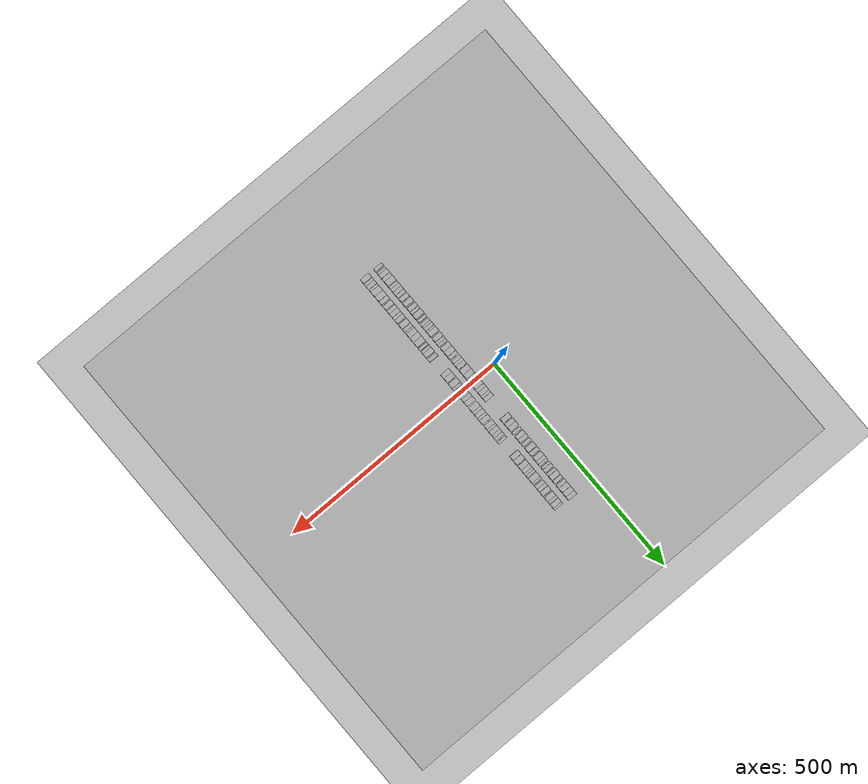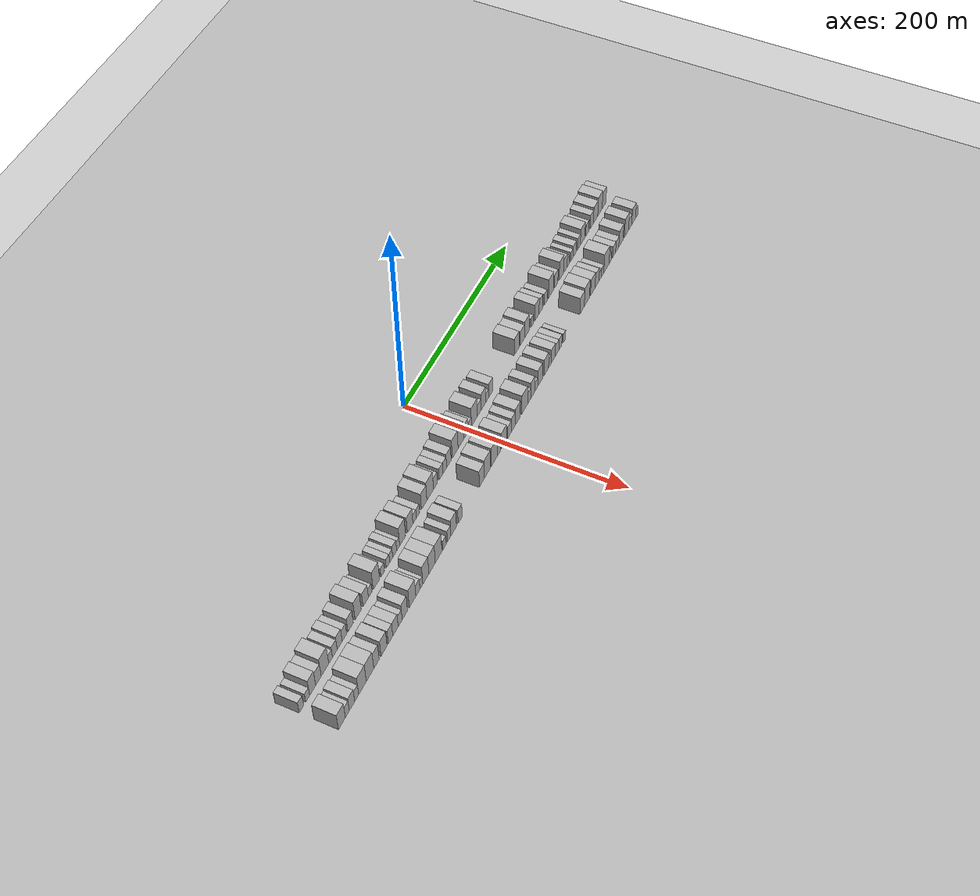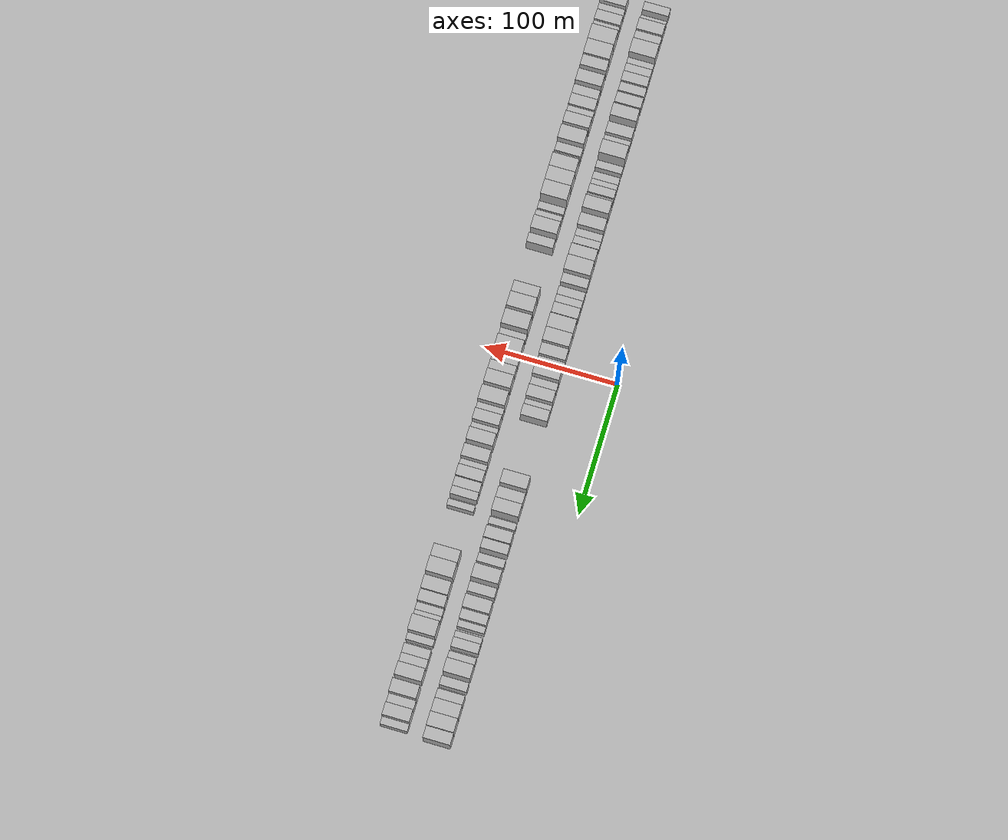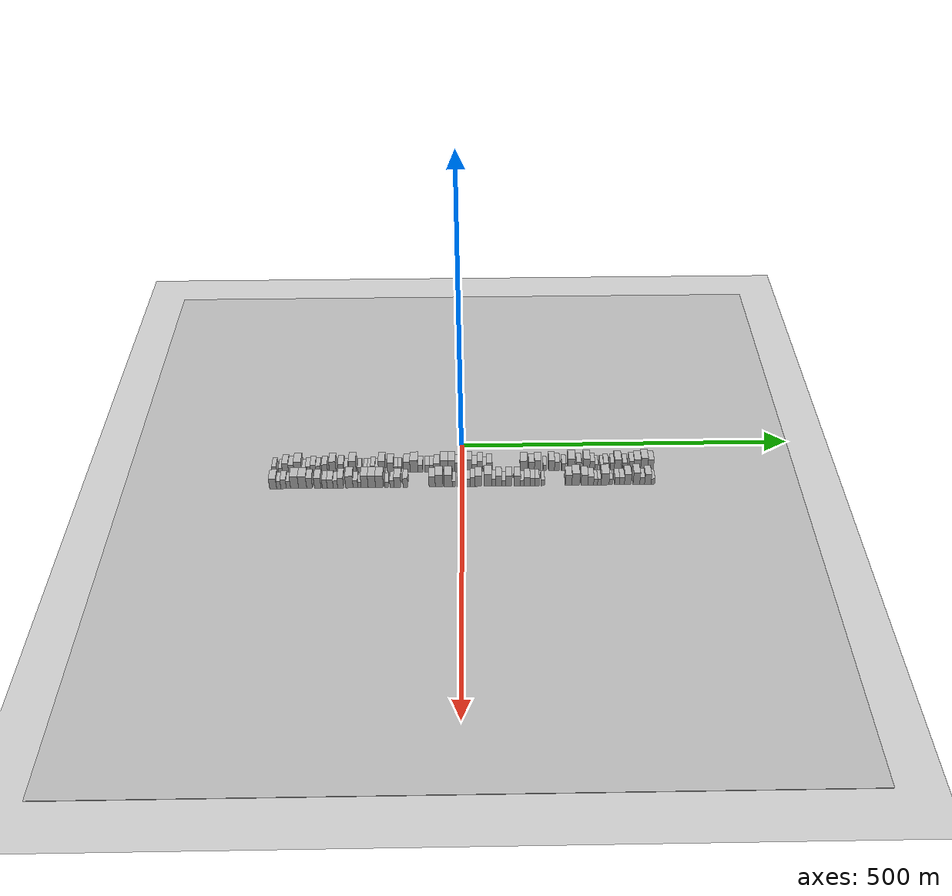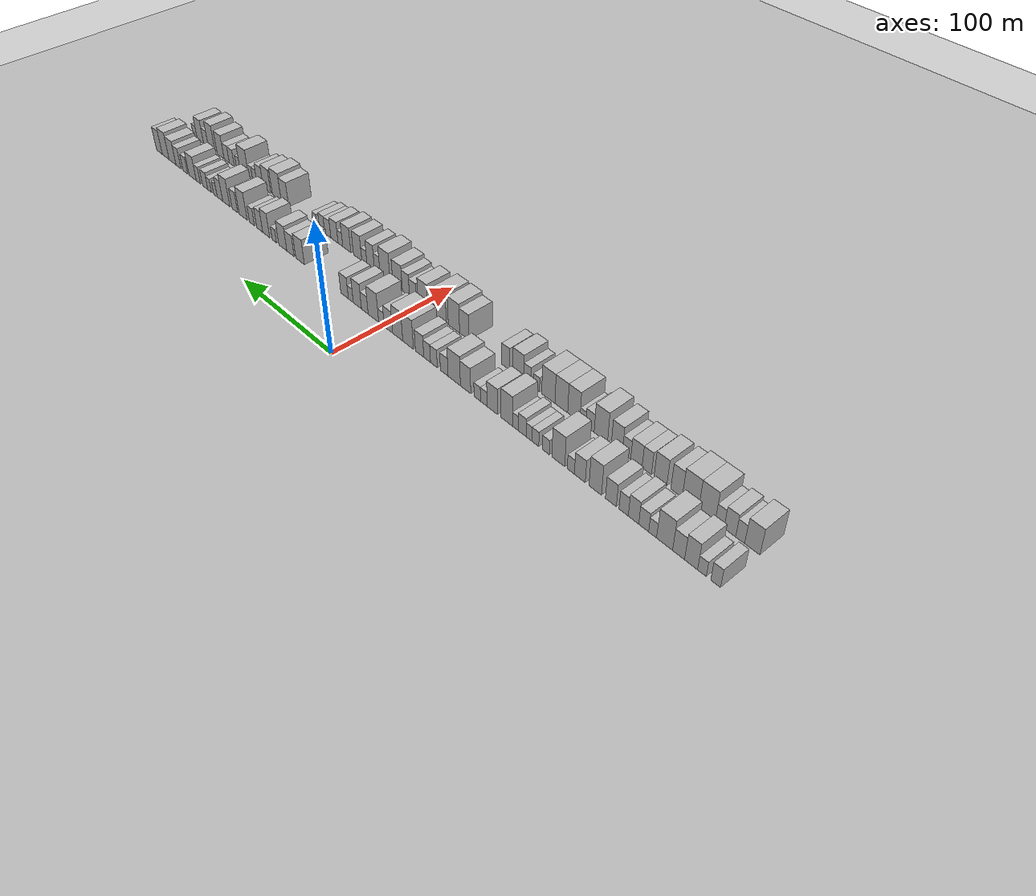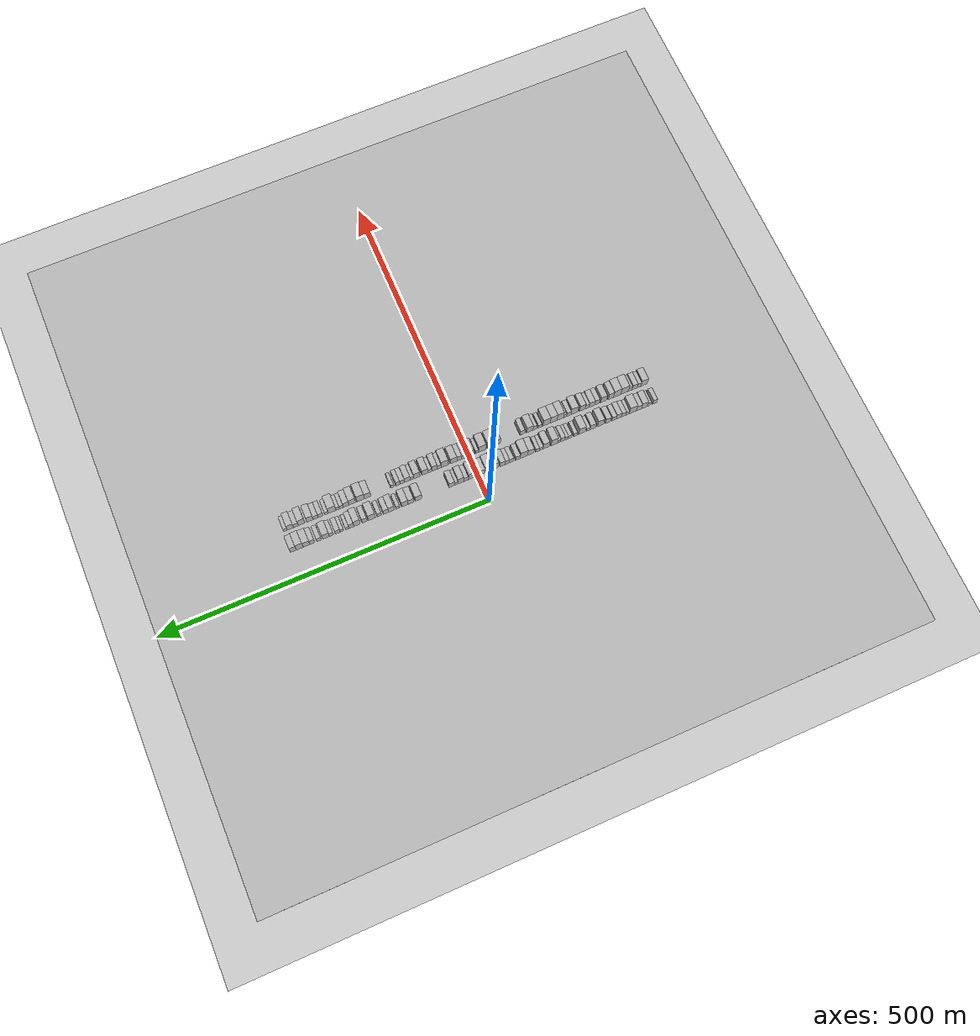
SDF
<?xml version="1.0" encoding="utf-8"?>

<sdf version="1.6">

   <world name="default">

      <gui fullscreen="0">

         <camera name="user_camera">

            <pose>-15 0 4.57585 0 0 0</pose>

            <view_controller>orbit</view_controller>

         </camera>

      </gui>

      <scene>

         <sky>

           <clouds>

             <speed>12</speed>

           </clouds>

         </sky>

         <ambient>0.4 0.4 0.4 1</ambient>

         <background>0.7 0.7 0.7 1</background>

         <shadows>1</shadows>

      </scene>

      <gravity>0 0 -9.8066</gravity>

      <magnetic_field>6e-06 2.3e-05 -4.2e-05</magnetic_field>

      <physics default="0" name="default_physics" type="ode">

         <ode>

            <solver>

               <type>quick</type>

               <iters>10</iters>

               <sor>1.0</sor>

               <use_dynamic_moi_rescaling>0</use_dynamic_moi_rescaling>

            </solver>

            <constraints>

               <cfm>0</cfm>

               <erp>0.2</erp>

               <contact_max_correcting_vel>100</contact_max_correcting_vel>

               <contact_surface_layer>0.001</contact_surface_layer>

            </constraints>

         </ode>

         <max_step_size>0.004</max_step_size>

         <real_time_factor>1</real_time_factor>

         <real_time_update_rate>250</real_time_update_rate>

      </physics>

      <light name="sun" type="directional">

         <cast_shadows>1</cast_shadows>

         <pose>0 0 10 0 0 0</pose>

         <diffuse>0.8 0.8 0.8 1</diffuse>

         <specular>0.2 0.2 0.2 1</specular>

         <attenuation>

            <range>1000</range>

            <constant>0.9</constant>

            <linear>0.01</linear>

            <quadratic>0.001</quadratic>

         </attenuation>

         <direction>-0.5 0.1 -0.9</direction>

      </light>

      <include>

         <name>ground_plane_1</name>

         <uri>model://HANNAS_ground_plane</uri>

         <pose>0 0 0  0 0 0</pose>

      </include>

      <include>

         <name>ground_plane_2</name>

         <uri>model://HANNAS_ground_plane</uri>

         <pose>100 0 0  0 0 0</pose>

      </include>

      <model name="building_1">

         <static>1</static>

         <pose frame="">50.0000 -280.6989 0 0.000000 0.000000 0.000000</pose>

         <link name="link">

            <pose frame="">0 0 7.50 0 0 0</pose>

            <collision name="collision">

               <geometry>

                  <box>

                     <size>20.0000 6.6021 15.0000</size>

                  </box>

               </geometry>

               <max_contacts>10</max_contacts>

               <surface>

                  <contact>

                     <ode/>

                  </contact>

                  <bounce/>

                  <friction>

                     <torsional>

                        <ode/>

                     </torsional>

                     <ode/>

                  </friction>

               </surface>

            </collision>

            <visual name="visual">

               <cast_shadows>0</cast_shadows>

               <geometry>

                  <box>

                     <size>20.0000 6.6021 15.0000</size>

                  </box>

               </geometry>

               <material>

                  <script>

                     <uri>model://HANNAS_wall/materials/scripts</uri>

                     <uri>model://HANNAS_wall/materials/textures</uri>

                     <name>vrc/HANNAS_wall</name>

                  </script>

               </material>

            </visual>

            <self_collide>0</self_collide>

            <enable_wind>0</enable_wind>

            <kinematic>0</kinematic>

         </link>

      </model>

      <model name="building_2">

         <static>1</static>

         <pose frame="">50.0000 -271.4203 0 0.000000 0.000000 0.000000</pose>

         <link name="link">

            <pose frame="">0 0 6.00 0 0 0</pose>

            <collision name="collision">

               <geometry>

                  <box>

                     <size>20.0000 5.9551 12.0000</size>

                  </box>

               </geometry>

               <max_contacts>10</max_contacts>

               <surface>

                  <contact>

                     <ode/>

                  </contact>

                  <bounce/>

                  <friction>

                     <torsional>

                        <ode/>

                     </torsional>

                     <ode/>

                  </friction>

               </surface>

            </collision>

            <visual name="visual">

               <cast_shadows>0</cast_shadows>

               <geometry>

                  <box>

                     <size>20.0000 5.9551 12.0000</size>

                  </box>

               </geometry>

               <material>

                  <script>

                     <uri>model://HANNAS_wall/materials/scripts</uri>

                     <uri>model://HANNAS_wall/materials/textures</uri>

                     <name>vrc/HANNAS_wall</name>

                  </script>

               </material>

            </visual>

            <self_collide>0</self_collide>

            <enable_wind>0</enable_wind>

            <kinematic>0</kinematic>

         </link>

      </model>

      <model name="building_3">

         <static>1</static>

         <pose frame="">50.0000 -263.9315 0 0.000000 0.000000 0.000000</pose>

         <link name="link">

            <pose frame="">0 0 10.50 0 0 0</pose>

            <collision name="collision">

               <geometry>

                  <box>

                     <size>20.0000 9.0226 21.0000</size>

                  </box>

               </geometry>

               <max_contacts>10</max_contacts>

               <surface>

                  <contact>

                     <ode/>

                  </contact>

                  <bounce/>

                  <friction>

                     <torsional>

                        <ode/>

                     </torsional>

                     <ode/>

                  </friction>

               </surface>

            </collision>

            <visual name="visual">

               <cast_shadows>0</cast_shadows>

               <geometry>

                  <box>

                     <size>20.0000 9.0226 21.0000</size>

                  </box>

               </geometry>

               <material>

                  <script>

                     <uri>model://HANNAS_wall/materials/scripts</uri>

                     <uri>model://HANNAS_wall/materials/textures</uri>

                     <name>vrc/HANNAS_wall</name>

                  </script>

               </material>

            </visual>

            <self_collide>0</self_collide>

            <enable_wind>0</enable_wind>

            <kinematic>0</kinematic>

         </link>

      </model>

      <model name="building_4">

         <static>1</static>

         <pose frame="">50.0000 -255.2241 0 0.000000 0.000000 0.000000</pose>

         <link name="link">

            <pose frame="">0 0 9.00 0 0 0</pose>

            <collision name="collision">

               <geometry>

                  <box>

                     <size>20.0000 8.3921 18.0000</size>

                  </box>

               </geometry>

               <max_contacts>10</max_contacts>

               <surface>

                  <contact>

                     <ode/>

                  </contact>

                  <bounce/>

                  <friction>

                     <torsional>

                        <ode/>

                     </torsional>

                     <ode/>

                  </friction>

               </surface>

            </collision>

            <visual name="visual">

               <cast_shadows>0</cast_shadows>

               <geometry>

                  <box>

                     <size>20.0000 8.3921 18.0000</size>

                  </box>

               </geometry>

               <material>

                  <script>

                     <uri>model://HANNAS_wall/materials/scripts</uri>

                     <uri>model://HANNAS_wall/materials/textures</uri>

                     <name>vrc/HANNAS_wall</name>

                  </script>

               </material>

            </visual>

            <self_collide>0</self_collide>

            <enable_wind>0</enable_wind>

            <kinematic>0</kinematic>

         </link>

      </model>

      <model name="building_5">

         <static>1</static>

         <pose frame="">50.0000 -245.2907 0 0.000000 0.000000 0.000000</pose>

         <link name="link">

            <pose frame="">0 0 12.00 0 0 0</pose>

            <collision name="collision">

               <geometry>

                  <box>

                     <size>20.0000 11.4748 24.0000</size>

                  </box>

               </geometry>

               <max_contacts>10</max_contacts>

               <surface>

                  <contact>

                     <ode/>

                  </contact>

                  <bounce/>

                  <friction>

                     <torsional>

                        <ode/>

                     </torsional>

                     <ode/>

                  </friction>

               </surface>

            </collision>

            <visual name="visual">

               <cast_shadows>0</cast_shadows>

               <geometry>

                  <box>

                     <size>20.0000 11.4748 24.0000</size>

                  </box>

               </geometry>

               <material>

                  <script>

                     <uri>model://HANNAS_wall/materials/scripts</uri>

                     <uri>model://HANNAS_wall/materials/textures</uri>

                     <name>vrc/HANNAS_wall</name>

                  </script>

               </material>

            </visual>

            <self_collide>0</self_collide>

            <enable_wind>0</enable_wind>

            <kinematic>0</kinematic>

         </link>

      </model>

      <model name="building_6">

         <static>1</static>

         <pose frame="">50.0000 -236.6807 0 0.000000 0.000000 0.000000</pose>

         <link name="link">

            <pose frame="">0 0 6.00 0 0 0</pose>

            <collision name="collision">

               <geometry>

                  <box>

                     <size>20.0000 5.7452 12.0000</size>

                  </box>

               </geometry>

               <max_contacts>10</max_contacts>

               <surface>

                  <contact>

                     <ode/>

                  </contact>

                  <bounce/>

                  <friction>

                     <torsional>

                        <ode/>

                     </torsional>

                     <ode/>

                  </friction>

               </surface>

            </collision>

            <visual name="visual">

               <cast_shadows>0</cast_shadows>

               <geometry>

                  <box>

                     <size>20.0000 5.7452 12.0000</size>

                  </box>

               </geometry>

               <material>

                  <script>

                     <uri>model://HANNAS_wall/materials/scripts</uri>

                     <uri>model://HANNAS_wall/materials/textures</uri>

                     <name>vrc/HANNAS_wall</name>

                  </script>

               </material>

            </visual>

            <self_collide>0</self_collide>

            <enable_wind>0</enable_wind>

            <kinematic>0</kinematic>

         </link>

      </model>

      <model name="building_7">

         <static>1</static>

         <pose frame="">50.0000 -230.1523 0 0.000000 0.000000 0.000000</pose>

         <link name="link">

            <pose frame="">0 0 7.50 0 0 0</pose>

            <collision name="collision">

               <geometry>

                  <box>

                     <size>20.0000 7.3116 15.0000</size>

                  </box>

               </geometry>

               <max_contacts>10</max_contacts>

               <surface>

                  <contact>

                     <ode/>

                  </contact>

                  <bounce/>

                  <friction>

                     <torsional>

                        <ode/>

                     </torsional>

                     <ode/>

                  </friction>

               </surface>

            </collision>

            <visual name="visual">

               <cast_shadows>0</cast_shadows>

               <geometry>

                  <box>

                     <size>20.0000 7.3116 15.0000</size>

                  </box>

               </geometry>

               <material>

                  <script>

                     <uri>model://HANNAS_wall/materials/scripts</uri>

                     <uri>model://HANNAS_wall/materials/textures</uri>

                     <name>vrc/HANNAS_wall</name>

                  </script>

               </material>

            </visual>

            <self_collide>0</self_collide>

            <enable_wind>0</enable_wind>

            <kinematic>0</kinematic>

         </link>

      </model>

      <model name="building_8">

         <static>1</static>

         <pose frame="">50.0000 -222.6213 0 0.000000 0.000000 0.000000</pose>

         <link name="link">

            <pose frame="">0 0 9.00 0 0 0</pose>

            <collision name="collision">

               <geometry>

                  <box>

                     <size>20.0000 7.7506 18.0000</size>

                  </box>

               </geometry>

               <max_contacts>10</max_contacts>

               <surface>

                  <contact>

                     <ode/>

                  </contact>

                  <bounce/>

                  <friction>

                     <torsional>

                        <ode/>

                     </torsional>

                     <ode/>

                  </friction>

               </surface>

            </collision>

            <visual name="visual">

               <cast_shadows>0</cast_shadows>

               <geometry>

                  <box>

                     <size>20.0000 7.7506 18.0000</size>

                  </box>

               </geometry>

               <material>

                  <script>

                     <uri>model://HANNAS_wall/materials/scripts</uri>

                     <uri>model://HANNAS_wall/materials/textures</uri>

                     <name>vrc/HANNAS_wall</name>

                  </script>

               </material>

            </visual>

            <self_collide>0</self_collide>

            <enable_wind>0</enable_wind>

            <kinematic>0</kinematic>

         </link>

      </model>

      <model name="building_9">

         <static>1</static>

         <pose frame="">50.0000 -215.2409 0 0.000000 0.000000 0.000000</pose>

         <link name="link">

            <pose frame="">0 0 7.50 0 0 0</pose>

            <collision name="collision">

               <geometry>

                  <box>

                     <size>20.0000 7.0102 15.0000</size>

                  </box>

               </geometry>

               <max_contacts>10</max_contacts>

               <surface>

                  <contact>

                     <ode/>

                  </contact>

                  <bounce/>

                  <friction>

                     <torsional>

                        <ode/>

                     </torsional>

                     <ode/>

                  </friction>

               </surface>

            </collision>

            <visual name="visual">

               <cast_shadows>0</cast_shadows>

               <geometry>

                  <box>

                     <size>20.0000 7.0102 15.0000</size>

                  </box>

               </geometry>

               <material>

                  <script>

                     <uri>model://HANNAS_wall/materials/scripts</uri>

                     <uri>model://HANNAS_wall/materials/textures</uri>

                     <name>vrc/HANNAS_wall</name>

                  </script>

               </material>

            </visual>

            <self_collide>0</self_collide>

            <enable_wind>0</enable_wind>

            <kinematic>0</kinematic>

         </link>

      </model>

      <model name="building_10">

         <static>1</static>

         <pose frame="">50.0000 -205.5315 0 0.000000 0.000000 0.000000</pose>

         <link name="link">

            <pose frame="">0 0 9.00 0 0 0</pose>

            <collision name="collision">

               <geometry>

                  <box>

                     <size>20.0000 8.4085 18.0000</size>

                  </box>

               </geometry>

               <max_contacts>10</max_contacts>

               <surface>

                  <contact>

                     <ode/>

                  </contact>

                  <bounce/>

                  <friction>

                     <torsional>

                        <ode/>

                     </torsional>

                     <ode/>

                  </friction>

               </surface>

            </collision>

            <visual name="visual">

               <cast_shadows>0</cast_shadows>

               <geometry>

                  <box>

                     <size>20.0000 8.4085 18.0000</size>

                  </box>

               </geometry>

               <material>

                  <script>

                     <uri>model://HANNAS_wall/materials/scripts</uri>

                     <uri>model://HANNAS_wall/materials/textures</uri>

                     <name>vrc/HANNAS_wall</name>

                  </script>

               </material>

            </visual>

            <self_collide>0</self_collide>

            <enable_wind>0</enable_wind>

            <kinematic>0</kinematic>

         </link>

      </model>

      <model name="building_11">

         <static>1</static>

         <pose frame="">50.0000 -193.4577 0 0.000000 0.000000 0.000000</pose>

         <link name="link">

            <pose frame="">0 0 12.00 0 0 0</pose>

            <collision name="collision">

               <geometry>

                  <box>

                     <size>20.0000 9.7391 24.0000</size>

                  </box>

               </geometry>

               <max_contacts>10</max_contacts>

               <surface>

                  <contact>

                     <ode/>

                  </contact>

                  <bounce/>

                  <friction>

                     <torsional>

                        <ode/>

                     </torsional>

                     <ode/>

                  </friction>

               </surface>

            </collision>

            <visual name="visual">

               <cast_shadows>0</cast_shadows>

               <geometry>

                  <box>

                     <size>20.0000 9.7391 24.0000</size>

                  </box>

               </geometry>

               <material>

                  <script>

                     <uri>model://HANNAS_wall/materials/scripts</uri>

                     <uri>model://HANNAS_wall/materials/textures</uri>

                     <name>vrc/HANNAS_wall</name>

                  </script>

               </material>

            </visual>

            <self_collide>0</self_collide>

            <enable_wind>0</enable_wind>

            <kinematic>0</kinematic>

         </link>

      </model>

      <model name="building_12">

         <static>1</static>

         <pose frame="">50.0000 -181.2519 0 0.000000 0.000000 0.000000</pose>

         <link name="link">

            <pose frame="">0 0 9.00 0 0 0</pose>

            <collision name="collision">

               <geometry>

                  <box>

                     <size>20.0000 8.6725 18.0000</size>

                  </box>

               </geometry>

               <max_contacts>10</max_contacts>

               <surface>

                  <contact>

                     <ode/>

                  </contact>

                  <bounce/>

                  <friction>

                     <torsional>

                        <ode/>

                     </torsional>

                     <ode/>

                  </friction>

               </surface>

            </collision>

            <visual name="visual">

               <cast_shadows>0</cast_shadows>

               <geometry>

                  <box>

                     <size>20.0000 8.6725 18.0000</size>

                  </box>

               </geometry>

               <material>

                  <script>

                     <uri>model://HANNAS_wall/materials/scripts</uri>

                     <uri>model://HANNAS_wall/materials/textures</uri>

                     <name>vrc/HANNAS_wall</name>

                  </script>

               </material>

            </visual>

            <self_collide>0</self_collide>

            <enable_wind>0</enable_wind>

            <kinematic>0</kinematic>

         </link>

      </model>

      <model name="building_13">

         <static>1</static>

         <pose frame="">50.0000 -174.0403 0 0.000000 0.000000 0.000000</pose>

         <link name="link">

            <pose frame="">0 0 6.00 0 0 0</pose>

            <collision name="collision">

               <geometry>

                  <box>

                     <size>20.0000 5.7507 12.0000</size>

                  </box>

               </geometry>

               <max_contacts>10</max_contacts>

               <surface>

                  <contact>

                     <ode/>

                  </contact>

                  <bounce/>

                  <friction>

                     <torsional>

                        <ode/>

                     </torsional>

                     <ode/>

                  </friction>

               </surface>

            </collision>

            <visual name="visual">

               <cast_shadows>0</cast_shadows>

               <geometry>

                  <box>

                     <size>20.0000 5.7507 12.0000</size>

                  </box>

               </geometry>

               <material>

                  <script>

                     <uri>model://HANNAS_wall/materials/scripts</uri>

                     <uri>model://HANNAS_wall/materials/textures</uri>

                     <name>vrc/HANNAS_wall</name>

                  </script>

               </material>

            </visual>

            <self_collide>0</self_collide>

            <enable_wind>0</enable_wind>

            <kinematic>0</kinematic>

         </link>

      </model>

      <model name="building_14">

         <static>1</static>

         <pose frame="">50.0000 -163.8417 0 0.000000 0.000000 0.000000</pose>

         <link name="link">

            <pose frame="">0 0 12.00 0 0 0</pose>

            <collision name="collision">

               <geometry>

                  <box>

                     <size>20.0000 10.6465 24.0000</size>

                  </box>

               </geometry>

               <max_contacts>10</max_contacts>

               <surface>

                  <contact>

                     <ode/>

                  </contact>

                  <bounce/>

                  <friction>

                     <torsional>

                        <ode/>

                     </torsional>

                     <ode/>

                  </friction>

               </surface>

            </collision>

            <visual name="visual">

               <cast_shadows>0</cast_shadows>

               <geometry>

                  <box>

                     <size>20.0000 10.6465 24.0000</size>

                  </box>

               </geometry>

               <material>

                  <script>

                     <uri>model://HANNAS_wall/materials/scripts</uri>

                     <uri>model://HANNAS_wall/materials/textures</uri>

                     <name>vrc/HANNAS_wall</name>

                  </script>

               </material>

            </visual>

            <self_collide>0</self_collide>

            <enable_wind>0</enable_wind>

            <kinematic>0</kinematic>

         </link>

      </model>

      <model name="building_15">

         <static>1</static>

         <pose frame="">50.0000 -153.5660 0 0.000000 0.000000 0.000000</pose>

         <link name="link">

            <pose frame="">0 0 6.00 0 0 0</pose>

            <collision name="collision">

               <geometry>

                  <box>

                     <size>20.0000 5.9048 12.0000</size>

                  </box>

               </geometry>

               <max_contacts>10</max_contacts>

               <surface>

                  <contact>

                     <ode/>

                  </contact>

                  <bounce/>

                  <friction>

                     <torsional>

                        <ode/>

                     </torsional>

                     <ode/>

                  </friction>

               </surface>

            </collision>

            <visual name="visual">

               <cast_shadows>0</cast_shadows>

               <geometry>

                  <box>

                     <size>20.0000 5.9048 12.0000</size>

                  </box>

               </geometry>

               <material>

                  <script>

                     <uri>model://HANNAS_wall/materials/scripts</uri>

                     <uri>model://HANNAS_wall/materials/textures</uri>

                     <name>vrc/HANNAS_wall</name>

                  </script>

               </material>

            </visual>

            <self_collide>0</self_collide>

            <enable_wind>0</enable_wind>

            <kinematic>0</kinematic>

         </link>

      </model>

      <model name="building_16">

         <static>1</static>

         <pose frame="">50.0000 -144.7277 0 0.000000 0.000000 0.000000</pose>

         <link name="link">

            <pose frame="">0 0 6.00 0 0 0</pose>

            <collision name="collision">

               <geometry>

                  <box>

                     <size>20.0000 5.7719 12.0000</size>

                  </box>

               </geometry>

               <max_contacts>10</max_contacts>

               <surface>

                  <contact>

                     <ode/>

                  </contact>

                  <bounce/>

                  <friction>

                     <torsional>

                        <ode/>

                     </torsional>

                     <ode/>

                  </friction>

               </surface>

            </collision>

            <visual name="visual">

               <cast_shadows>0</cast_shadows>

               <geometry>

                  <box>

                     <size>20.0000 5.7719 12.0000</size>

                  </box>

               </geometry>

               <material>

                  <script>

                     <uri>model://HANNAS_wall/materials/scripts</uri>

                     <uri>model://HANNAS_wall/materials/textures</uri>

                     <name>vrc/HANNAS_wall</name>

                  </script>

               </material>

            </visual>

            <self_collide>0</self_collide>

            <enable_wind>0</enable_wind>

            <kinematic>0</kinematic>

         </link>

      </model>

      <model name="building_17">

         <static>1</static>

         <pose frame="">50.0000 -139.3136 0 0.000000 0.000000 0.000000</pose>

         <link name="link">

            <pose frame="">0 0 6.00 0 0 0</pose>

            <collision name="collision">

               <geometry>

                  <box>

                     <size>20.0000 5.0563 12.0000</size>

                  </box>

               </geometry>

               <max_contacts>10</max_contacts>

               <surface>

                  <contact>

                     <ode/>

                  </contact>

                  <bounce/>

                  <friction>

                     <torsional>

                        <ode/>

                     </torsional>

                     <ode/>

                  </friction>

               </surface>

            </collision>

            <visual name="visual">

               <cast_shadows>0</cast_shadows>

               <geometry>

                  <box>

                     <size>20.0000 5.0563 12.0000</size>

                  </box>

               </geometry>

               <material>

                  <script>

                     <uri>model://HANNAS_wall/materials/scripts</uri>

                     <uri>model://HANNAS_wall/materials/textures</uri>

                     <name>vrc/HANNAS_wall</name>

                  </script>

               </material>

            </visual>

            <self_collide>0</self_collide>

            <enable_wind>0</enable_wind>

            <kinematic>0</kinematic>

         </link>

      </model>

      <model name="building_18">

         <static>1</static>

         <pose frame="">50.0000 -133.4792 0 0.000000 0.000000 0.000000</pose>

         <link name="link">

            <pose frame="">0 0 7.50 0 0 0</pose>

            <collision name="collision">

               <geometry>

                  <box>

                     <size>20.0000 6.6124 15.0000</size>

                  </box>

               </geometry>

               <max_contacts>10</max_contacts>

               <surface>

                  <contact>

                     <ode/>

                  </contact>

                  <bounce/>

                  <friction>

                     <torsional>

                        <ode/>

                     </torsional>

                     <ode/>

                  </friction>

               </surface>

            </collision>

            <visual name="visual">

               <cast_shadows>0</cast_shadows>

               <geometry>

                  <box>

                     <size>20.0000 6.6124 15.0000</size>

                  </box>

               </geometry>

               <material>

                  <script>

                     <uri>model://HANNAS_wall/materials/scripts</uri>

                     <uri>model://HANNAS_wall/materials/textures</uri>

                     <name>vrc/HANNAS_wall</name>

                  </script>

               </material>

            </visual>

            <self_collide>0</self_collide>

            <enable_wind>0</enable_wind>

            <kinematic>0</kinematic>

         </link>

      </model>

      <model name="building_19">

         <static>1</static>

         <pose frame="">50.0000 -127.5917 0 0.000000 0.000000 0.000000</pose>

         <link name="link">

            <pose frame="">0 0 6.00 0 0 0</pose>

            <collision name="collision">

               <geometry>

                  <box>

                     <size>20.0000 5.1625 12.0000</size>

                  </box>

               </geometry>

               <max_contacts>10</max_contacts>

               <surface>

                  <contact>

                     <ode/>

                  </contact>

                  <bounce/>

                  <friction>

                     <torsional>

                        <ode/>

                     </torsional>

                     <ode/>

                  </friction>

               </surface>

            </collision>

            <visual name="visual">

               <cast_shadows>0</cast_shadows>

               <geometry>

                  <box>

                     <size>20.0000 5.1625 12.0000</size>

                  </box>

               </geometry>

               <material>

                  <script>

                     <uri>model://HANNAS_wall/materials/scripts</uri>

                     <uri>model://HANNAS_wall/materials/textures</uri>

                     <name>vrc/HANNAS_wall</name>

                  </script>

               </material>

            </visual>

            <self_collide>0</self_collide>

            <enable_wind>0</enable_wind>

            <kinematic>0</kinematic>

         </link>

      </model>

      <model name="building_20">

         <static>1</static>

         <pose frame="">50.0000 -119.9798 0 0.000000 0.000000 0.000000</pose>

         <link name="link">

            <pose frame="">0 0 12.00 0 0 0</pose>

            <collision name="collision">

               <geometry>

                  <box>

                     <size>20.0000 10.0615 24.0000</size>

                  </box>

               </geometry>

               <max_contacts>10</max_contacts>

               <surface>

                  <contact>

                     <ode/>

                  </contact>

                  <bounce/>

                  <friction>

                     <torsional>

                        <ode/>

                     </torsional>

                     <ode/>

                  </friction>

               </surface>

            </collision>

            <visual name="visual">

               <cast_shadows>0</cast_shadows>

               <geometry>

                  <box>

                     <size>20.0000 10.0615 24.0000</size>

                  </box>

               </geometry>

               <material>

                  <script>

                     <uri>model://HANNAS_wall/materials/scripts</uri>

                     <uri>model://HANNAS_wall/materials/textures</uri>

                     <name>vrc/HANNAS_wall</name>

                  </script>

               </material>

            </visual>

            <self_collide>0</self_collide>

            <enable_wind>0</enable_wind>

            <kinematic>0</kinematic>

         </link>

      </model>

      <model name="building_21">

         <static>1</static>

         <pose frame="">50.0000 -107.1472 0 0.000000 0.000000 0.000000</pose>

         <link name="link">

            <pose frame="">0 0 10.50 0 0 0</pose>

            <collision name="collision">

               <geometry>

                  <box>

                     <size>20.0000 9.6036 21.0000</size>

                  </box>

               </geometry>

               <max_contacts>10</max_contacts>

               <surface>

                  <contact>

                     <ode/>

                  </contact>

                  <bounce/>

                  <friction>

                     <torsional>

                        <ode/>

                     </torsional>

                     <ode/>

                  </friction>

               </surface>

            </collision>

            <visual name="visual">

               <cast_shadows>0</cast_shadows>

               <geometry>

                  <box>

                     <size>20.0000 9.6036 21.0000</size>

                  </box>

               </geometry>

               <material>

                  <script>

                     <uri>model://HANNAS_wall/materials/scripts</uri>

                     <uri>model://HANNAS_wall/materials/textures</uri>

                     <name>vrc/HANNAS_wall</name>

                  </script>

               </material>

            </visual>

            <self_collide>0</self_collide>

            <enable_wind>0</enable_wind>

            <kinematic>0</kinematic>

         </link>

      </model>

      <model name="building_22">

         <static>1</static>

         <pose frame="">50.0000 -99.4069 0 0.000000 0.000000 0.000000</pose>

         <link name="link">

            <pose frame="">0 0 6.00 0 0 0</pose>

            <collision name="collision">

               <geometry>

                  <box>

                     <size>20.0000 5.8770 12.0000</size>

                  </box>

               </geometry>

               <max_contacts>10</max_contacts>

               <surface>

                  <contact>

                     <ode/>

                  </contact>

                  <bounce/>

                  <friction>

                     <torsional>

                        <ode/>

                     </torsional>

                     <ode/>

                  </friction>

               </surface>

            </collision>

            <visual name="visual">

               <cast_shadows>0</cast_shadows>

               <geometry>

                  <box>

                     <size>20.0000 5.8770 12.0000</size>

                  </box>

               </geometry>

               <material>

                  <script>

                     <uri>model://HANNAS_wall/materials/scripts</uri>

                     <uri>model://HANNAS_wall/materials/textures</uri>

                     <name>vrc/HANNAS_wall</name>

                  </script>

               </material>

            </visual>

            <self_collide>0</self_collide>

            <enable_wind>0</enable_wind>

            <kinematic>0</kinematic>

         </link>

      </model>

      <model name="building_23">

         <static>1</static>

         <pose frame="">50.0000 -93.5156 0 0.000000 0.000000 0.000000</pose>

         <link name="link">

            <pose frame="">0 0 6.00 0 0 0</pose>

            <collision name="collision">

               <geometry>

                  <box>

                     <size>20.0000 5.9058 12.0000</size>

                  </box>

               </geometry>

               <max_contacts>10</max_contacts>

               <surface>

                  <contact>

                     <ode/>

                  </contact>

                  <bounce/>

                  <friction>

                     <torsional>

                        <ode/>

                     </torsional>

                     <ode/>

                  </friction>

               </surface>

            </collision>

            <visual name="visual">

               <cast_shadows>0</cast_shadows>

               <geometry>

                  <box>

                     <size>20.0000 5.9058 12.0000</size>

                  </box>

               </geometry>

               <material>

                  <script>

                     <uri>model://HANNAS_wall/materials/scripts</uri>

                     <uri>model://HANNAS_wall/materials/textures</uri>

                     <name>vrc/HANNAS_wall</name>

                  </script>

               </material>

            </visual>

            <self_collide>0</self_collide>

            <enable_wind>0</enable_wind>

            <kinematic>0</kinematic>

         </link>

      </model>

      <model name="building_24">

         <static>1</static>

         <pose frame="">50.0000 -82.7268 0 0.000000 0.000000 0.000000</pose>

         <link name="link">

            <pose frame="">0 0 10.50 0 0 0</pose>

            <collision name="collision">

               <geometry>

                  <box>

                     <size>20.0000 9.6717 21.0000</size>

                  </box>

               </geometry>

               <max_contacts>10</max_contacts>

               <surface>

                  <contact>

                     <ode/>

                  </contact>

                  <bounce/>

                  <friction>

                     <torsional>

                        <ode/>

                     </torsional>

                     <ode/>

                  </friction>

               </surface>

            </collision>

            <visual name="visual">

               <cast_shadows>0</cast_shadows>

               <geometry>

                  <box>

                     <size>20.0000 9.6717 21.0000</size>

                  </box>

               </geometry>

               <material>

                  <script>

                     <uri>model://HANNAS_wall/materials/scripts</uri>

                     <uri>model://HANNAS_wall/materials/textures</uri>

                     <name>vrc/HANNAS_wall</name>

                  </script>

               </material>

            </visual>

            <self_collide>0</self_collide>

            <enable_wind>0</enable_wind>

            <kinematic>0</kinematic>

         </link>

      </model>

      <model name="building_25">

         <static>1</static>

         <pose frame="">50.0000 -72.0523 0 0.000000 0.000000 0.000000</pose>

         <link name="link">

            <pose frame="">0 0 12.00 0 0 0</pose>

            <collision name="collision">

               <geometry>

                  <box>

                     <size>20.0000 11.6772 24.0000</size>

                  </box>

               </geometry>

               <max_contacts>10</max_contacts>

               <surface>

                  <contact>

                     <ode/>

                  </contact>

                  <bounce/>

                  <friction>

                     <torsional>

                        <ode/>

                     </torsional>

                     <ode/>

                  </friction>

               </surface>

            </collision>

            <visual name="visual">

               <cast_shadows>0</cast_shadows>

               <geometry>

                  <box>

                     <size>20.0000 11.6772 24.0000</size>

                  </box>

               </geometry>

               <material>

                  <script>

                     <uri>model://HANNAS_wall/materials/scripts</uri>

                     <uri>model://HANNAS_wall/materials/textures</uri>

                     <name>vrc/HANNAS_wall</name>

                  </script>

               </material>

            </visual>

            <self_collide>0</self_collide>

            <enable_wind>0</enable_wind>

            <kinematic>0</kinematic>

         </link>

      </model>

      <model name="building_26">

         <static>1</static>

         <pose frame="">50.0000 -62.5154 0 0.000000 0.000000 0.000000</pose>

         <link name="link">

            <pose frame="">0 0 7.50 0 0 0</pose>

            <collision name="collision">

               <geometry>

                  <box>

                     <size>20.0000 7.3966 15.0000</size>

                  </box>

               </geometry>

               <max_contacts>10</max_contacts>

               <surface>

                  <contact>

                     <ode/>

                  </contact>

                  <bounce/>

                  <friction>

                     <torsional>

                        <ode/>

                     </torsional>

                     <ode/>

                  </friction>

               </surface>

            </collision>

            <visual name="visual">

               <cast_shadows>0</cast_shadows>

               <geometry>

                  <box>

                     <size>20.0000 7.3966 15.0000</size>

                  </box>

               </geometry>

               <material>

                  <script>

                     <uri>model://HANNAS_wall/materials/scripts</uri>

                     <uri>model://HANNAS_wall/materials/textures</uri>

                     <name>vrc/HANNAS_wall</name>

                  </script>

               </material>

            </visual>

            <self_collide>0</self_collide>

            <enable_wind>0</enable_wind>

            <kinematic>0</kinematic>

         </link>

      </model>

      <model name="building_27">

         <static>1</static>

         <pose frame="">50.0000 -52.4960 0 0.000000 0.000000 0.000000</pose>

         <link name="link">

            <pose frame="">0 0 7.50 0 0 0</pose>

            <collision name="collision">

               <geometry>

                  <box>

                     <size>20.0000 6.6422 15.0000</size>

                  </box>

               </geometry>

               <max_contacts>10</max_contacts>

               <surface>

                  <contact>

                     <ode/>

                  </contact>

                  <bounce/>

                  <friction>

                     <torsional>

                        <ode/>

                     </torsional>

                     <ode/>

                  </friction>

               </surface>

            </collision>

            <visual name="visual">

               <cast_shadows>0</cast_shadows>

               <geometry>

                  <box>

                     <size>20.0000 6.6422 15.0000</size>

                  </box>

               </geometry>

               <material>

                  <script>

                     <uri>model://HANNAS_wall/materials/scripts</uri>

                     <uri>model://HANNAS_wall/materials/textures</uri>

                     <name>vrc/HANNAS_wall</name>

                  </script>

               </material>

            </visual>

            <self_collide>0</self_collide>

            <enable_wind>0</enable_wind>

            <kinematic>0</kinematic>

         </link>

      </model>

      <model name="building_28">

         <static>1</static>

         <pose frame="">50.0000 -45.8515 0 0.000000 0.000000 0.000000</pose>

         <link name="link">

            <pose frame="">0 0 7.50 0 0 0</pose>

            <collision name="collision">

               <geometry>

                  <box>

                     <size>20.0000 6.6469 15.0000</size>

                  </box>

               </geometry>

               <max_contacts>10</max_contacts>

               <surface>

                  <contact>

                     <ode/>

                  </contact>

                  <bounce/>

                  <friction>

                     <torsional>

                        <ode/>

                     </torsional>

                     <ode/>

                  </friction>

               </surface>

            </collision>

            <visual name="visual">

               <cast_shadows>0</cast_shadows>

               <geometry>

                  <box>

                     <size>20.0000 6.6469 15.0000</size>

                  </box>

               </geometry>

               <material>

                  <script>

                     <uri>model://HANNAS_wall/materials/scripts</uri>

                     <uri>model://HANNAS_wall/materials/textures</uri>

                     <name>vrc/HANNAS_wall</name>

                  </script>

               </material>

            </visual>

            <self_collide>0</self_collide>

            <enable_wind>0</enable_wind>

            <kinematic>0</kinematic>

         </link>

      </model>

      <model name="building_29">

         <static>1</static>

         <pose frame="">50.0000 -38.3712 0 0.000000 0.000000 0.000000</pose>

         <link name="link">

            <pose frame="">0 0 9.00 0 0 0</pose>

            <collision name="collision">

               <geometry>

                  <box>

                     <size>20.0000 8.3137 18.0000</size>

                  </box>

               </geometry>

               <max_contacts>10</max_contacts>

               <surface>

                  <contact>

                     <ode/>

                  </contact>

                  <bounce/>

                  <friction>

                     <torsional>

                        <ode/>

                     </torsional>

                     <ode/>

                  </friction>

               </surface>

            </collision>

            <visual name="visual">

               <cast_shadows>0</cast_shadows>

               <geometry>

                  <box>

                     <size>20.0000 8.3137 18.0000</size>

                  </box>

               </geometry>

               <material>

                  <script>

                     <uri>model://HANNAS_wall/materials/scripts</uri>

                     <uri>model://HANNAS_wall/materials/textures</uri>

                     <name>vrc/HANNAS_wall</name>

                  </script>

               </material>

            </visual>

            <self_collide>0</self_collide>

            <enable_wind>0</enable_wind>

            <kinematic>0</kinematic>

         </link>

      </model>

      <model name="building_30">

         <static>1</static>

         <pose frame="">50.0000 -26.8099 0 0.000000 0.000000 0.000000</pose>

         <link name="link">

            <pose frame="">0 0 12.00 0 0 0</pose>

            <collision name="collision">

               <geometry>

                  <box>

                     <size>20.0000 10.8089 24.0000</size>

                  </box>

               </geometry>

               <max_contacts>10</max_contacts>

               <surface>

                  <contact>

                     <ode/>

                  </contact>

                  <bounce/>

                  <friction>

                     <torsional>

                        <ode/>

                     </torsional>

                     <ode/>

                  </friction>

               </surface>

            </collision>

            <visual name="visual">

               <cast_shadows>0</cast_shadows>

               <geometry>

                  <box>

                     <size>20.0000 10.8089 24.0000</size>

                  </box>

               </geometry>

               <material>

                  <script>

                     <uri>model://HANNAS_wall/materials/scripts</uri>

                     <uri>model://HANNAS_wall/materials/textures</uri>

                     <name>vrc/HANNAS_wall</name>

                  </script>

               </material>

            </visual>

            <self_collide>0</self_collide>

            <enable_wind>0</enable_wind>

            <kinematic>0</kinematic>

         </link>

      </model>

      <model name="building_31">

         <static>1</static>

         <pose frame="">50.0000 -16.1698 0 0.000000 0.000000 0.000000</pose>

         <link name="link">

            <pose frame="">0 0 12.00 0 0 0</pose>

            <collision name="collision">

               <geometry>

                  <box>

                     <size>20.0000 10.4713 24.0000</size>

                  </box>

               </geometry>

               <max_contacts>10</max_contacts>

               <surface>

                  <contact>

                     <ode/>

                  </contact>

                  <bounce/>

                  <friction>

                     <torsional>

                        <ode/>

                     </torsional>

                     <ode/>

                  </friction>

               </surface>

            </collision>

            <visual name="visual">

               <cast_shadows>0</cast_shadows>

               <geometry>

                  <box>

                     <size>20.0000 10.4713 24.0000</size>

                  </box>

               </geometry>

               <material>

                  <script>

                     <uri>model://HANNAS_wall/materials/scripts</uri>

                     <uri>model://HANNAS_wall/materials/textures</uri>

                     <name>vrc/HANNAS_wall</name>

                  </script>

               </material>

            </visual>

            <self_collide>0</self_collide>

            <enable_wind>0</enable_wind>

            <kinematic>0</kinematic>

         </link>

      </model>

      <model name="building_32">

         <static>1</static>

         <pose frame="">50.0000 -6.5407 0 0.000000 0.000000 0.000000</pose>

         <link name="link">

            <pose frame="">0 0 9.00 0 0 0</pose>

            <collision name="collision">

               <geometry>

                  <box>

                     <size>20.0000 8.7869 18.0000</size>

                  </box>

               </geometry>

               <max_contacts>10</max_contacts>

               <surface>

                  <contact>

                     <ode/>

                  </contact>

                  <bounce/>

                  <friction>

                     <torsional>

                        <ode/>

                     </torsional>

                     <ode/>

                  </friction>

               </surface>

            </collision>

            <visual name="visual">

               <cast_shadows>0</cast_shadows>

               <geometry>

                  <box>

                     <size>20.0000 8.7869 18.0000</size>

                  </box>

               </geometry>

               <material>

                  <script>

                     <uri>model://HANNAS_wall/materials/scripts</uri>

                     <uri>model://HANNAS_wall/materials/textures</uri>

                     <name>vrc/HANNAS_wall</name>

                  </script>

               </material>

            </visual>

            <self_collide>0</self_collide>

            <enable_wind>0</enable_wind>

            <kinematic>0</kinematic>

         </link>

      </model>

      <model name="building_33">

         <static>1</static>

         <pose frame="">50.0000 0.7738 0 0.000000 0.000000 0.000000</pose>

         <link name="link">

            <pose frame="">0 0 6.00 0 0 0</pose>

            <collision name="collision">

               <geometry>

                  <box>

                     <size>20.0000 5.8419 12.0000</size>

                  </box>

               </geometry>

               <max_contacts>10</max_contacts>

               <surface>

                  <contact>

                     <ode/>

                  </contact>

                  <bounce/>

                  <friction>

                     <torsional>

                        <ode/>

                     </torsional>

                     <ode/>

                  </friction>

               </surface>

            </collision>

            <visual name="visual">

               <cast_shadows>0</cast_shadows>

               <geometry>

                  <box>

                     <size>20.0000 5.8419 12.0000</size>

                  </box>

               </geometry>

               <material>

                  <script>

                     <uri>model://HANNAS_wall/materials/scripts</uri>

                     <uri>model://HANNAS_wall/materials/textures</uri>

                     <name>vrc/HANNAS_wall</name>

                  </script>

               </material>

            </visual>

            <self_collide>0</self_collide>

            <enable_wind>0</enable_wind>

            <kinematic>0</kinematic>

         </link>

      </model>

      <model name="building_34">

         <static>1</static>

         <pose frame="">50.0000 9.2958 0 0.000000 0.000000 0.000000</pose>

         <link name="link">

            <pose frame="">0 0 12.00 0 0 0</pose>

            <collision name="collision">

               <geometry>

                  <box>

                     <size>20.0000 11.2023 24.0000</size>

                  </box>

               </geometry>

               <max_contacts>10</max_contacts>

               <surface>

                  <contact>

                     <ode/>

                  </contact>

                  <bounce/>

                  <friction>

                     <torsional>

                        <ode/>

                     </torsional>

                     <ode/>

                  </friction>

               </surface>

            </collision>

            <visual name="visual">

               <cast_shadows>0</cast_shadows>

               <geometry>

                  <box>

                     <size>20.0000 11.2023 24.0000</size>

                  </box>

               </geometry>

               <material>

                  <script>

                     <uri>model://HANNAS_wall/materials/scripts</uri>

                     <uri>model://HANNAS_wall/materials/textures</uri>

                     <name>vrc/HANNAS_wall</name>

                  </script>

               </material>

            </visual>

            <self_collide>0</self_collide>

            <enable_wind>0</enable_wind>

            <kinematic>0</kinematic>

         </link>

      </model>

      <model name="building_35">

         <static>1</static>

         <pose frame="">50.0000 18.5480 0 0.000000 0.000000 0.000000</pose>

         <link name="link">

            <pose frame="">0 0 7.50 0 0 0</pose>

            <collision name="collision">

               <geometry>

                  <box>

                     <size>20.0000 7.3020 15.0000</size>

                  </box>

               </geometry>

               <max_contacts>10</max_contacts>

               <surface>

                  <contact>

                     <ode/>

                  </contact>

                  <bounce/>

                  <friction>

                     <torsional>

                        <ode/>

                     </torsional>

                     <ode/>

                  </friction>

               </surface>

            </collision>

            <visual name="visual">

               <cast_shadows>0</cast_shadows>

               <geometry>

                  <box>

                     <size>20.0000 7.3020 15.0000</size>

                  </box>

               </geometry>

               <material>

                  <script>

                     <uri>model://HANNAS_wall/materials/scripts</uri>

                     <uri>model://HANNAS_wall/materials/textures</uri>

                     <name>vrc/HANNAS_wall</name>

                  </script>

               </material>

            </visual>

            <self_collide>0</self_collide>

            <enable_wind>0</enable_wind>

            <kinematic>0</kinematic>

         </link>

      </model>

      <model name="building_36">

         <static>1</static>

         <pose frame="">50.0000 26.6706 0 0.000000 0.000000 0.000000</pose>

         <link name="link">

            <pose frame="">0 0 10.50 0 0 0</pose>

            <collision name="collision">

               <geometry>

                  <box>

                     <size>20.0000 8.9432 21.0000</size>

                  </box>

               </geometry>

               <max_contacts>10</max_contacts>

               <surface>

                  <contact>

                     <ode/>

                  </contact>

                  <bounce/>

                  <friction>

                     <torsional>

                        <ode/>

                     </torsional>

                     <ode/>

                  </friction>

               </surface>

            </collision>

            <visual name="visual">

               <cast_shadows>0</cast_shadows>

               <geometry>

                  <box>

                     <size>20.0000 8.9432 21.0000</size>

                  </box>

               </geometry>

               <material>

                  <script>

                     <uri>model://HANNAS_wall/materials/scripts</uri>

                     <uri>model://HANNAS_wall/materials/textures</uri>

                     <name>vrc/HANNAS_wall</name>

                  </script>

               </material>

            </visual>

            <self_collide>0</self_collide>

            <enable_wind>0</enable_wind>

            <kinematic>0</kinematic>

         </link>

      </model>

      <model name="building_37">

         <static>1</static>

         <pose frame="">50.0000 33.8603 0 0.000000 0.000000 0.000000</pose>

         <link name="link">

            <pose frame="">0 0 6.00 0 0 0</pose>

            <collision name="collision">

               <geometry>

                  <box>

                     <size>20.0000 5.4363 12.0000</size>

                  </box>

               </geometry>

               <max_contacts>10</max_contacts>

               <surface>

                  <contact>

                     <ode/>

                  </contact>

                  <bounce/>

                  <friction>

                     <torsional>

                        <ode/>

                     </torsional>

                     <ode/>

                  </friction>

               </surface>

            </collision>

            <visual name="visual">

               <cast_shadows>0</cast_shadows>

               <geometry>

                  <box>

                     <size>20.0000 5.4363 12.0000</size>

                  </box>

               </geometry>

               <material>

                  <script>

                     <uri>model://HANNAS_wall/materials/scripts</uri>

                     <uri>model://HANNAS_wall/materials/textures</uri>

                     <name>vrc/HANNAS_wall</name>

                  </script>

               </material>

            </visual>

            <self_collide>0</self_collide>

            <enable_wind>0</enable_wind>

            <kinematic>0</kinematic>

         </link>

      </model>

      <model name="building_38">

         <static>1</static>

         <pose frame="">50.0000 40.8012 0 0.000000 0.000000 0.000000</pose>

         <link name="link">

            <pose frame="">0 0 9.00 0 0 0</pose>

            <collision name="collision">

               <geometry>

                  <box>

                     <size>20.0000 8.4455 18.0000</size>

                  </box>

               </geometry>

               <max_contacts>10</max_contacts>

               <surface>

                  <contact>

                     <ode/>

                  </contact>

                  <bounce/>

                  <friction>

                     <torsional>

                        <ode/>

                     </torsional>

                     <ode/>

                  </friction>

               </surface>

            </collision>

            <visual name="visual">

               <cast_shadows>0</cast_shadows>

               <geometry>

                  <box>

                     <size>20.0000 8.4455 18.0000</size>

                  </box>

               </geometry>

               <material>

                  <script>

                     <uri>model://HANNAS_wall/materials/scripts</uri>

                     <uri>model://HANNAS_wall/materials/textures</uri>

                     <name>vrc/HANNAS_wall</name>

                  </script>

               </material>

            </visual>

            <self_collide>0</self_collide>

            <enable_wind>0</enable_wind>

            <kinematic>0</kinematic>

         </link>

      </model>

      <model name="building_39">

         <static>1</static>

         <pose frame="">50.0000 92.3838 0 0.000000 0.000000 0.000000</pose>

         <link name="link">

            <pose frame="">0 0 10.50 0 0 0</pose>

            <collision name="collision">

               <geometry>

                  <box>

                     <size>20.0000 10.2399 21.0000</size>

                  </box>

               </geometry>

               <max_contacts>10</max_contacts>

               <surface>

                  <contact>

                     <ode/>

                  </contact>

                  <bounce/>

                  <friction>

                     <torsional>

                        <ode/>

                     </torsional>

                     <ode/>

                  </friction>

               </surface>

            </collision>

            <visual name="visual">

               <cast_shadows>0</cast_shadows>

               <geometry>

                  <box>

                     <size>20.0000 10.2399 21.0000</size>

                  </box>

               </geometry>

               <material>

                  <script>

                     <uri>model://HANNAS_wall/materials/scripts</uri>

                     <uri>model://HANNAS_wall/materials/textures</uri>

                     <name>vrc/HANNAS_wall</name>

                  </script>

               </material>

            </visual>

            <self_collide>0</self_collide>

            <enable_wind>0</enable_wind>

            <kinematic>0</kinematic>

         </link>

      </model>

      <model name="building_40">

         <static>1</static>

         <pose frame="">50.0000 103.9644 0 0.000000 0.000000 0.000000</pose>

         <link name="link">

            <pose frame="">0 0 9.00 0 0 0</pose>

            <collision name="collision">

               <geometry>

                  <box>

                     <size>20.0000 8.9212 18.0000</size>

                  </box>

               </geometry>

               <max_contacts>10</max_contacts>

               <surface>

                  <contact>

                     <ode/>

                  </contact>

                  <bounce/>

                  <friction>

                     <torsional>

                        <ode/>

                     </torsional>

                     <ode/>

                  </friction>

               </surface>

            </collision>

            <visual name="visual">

               <cast_shadows>0</cast_shadows>

               <geometry>

                  <box>

                     <size>20.0000 8.9212 18.0000</size>

                  </box>

               </geometry>

               <material>

                  <script>

                     <uri>model://HANNAS_wall/materials/scripts</uri>

                     <uri>model://HANNAS_wall/materials/textures</uri>

                     <name>vrc/HANNAS_wall</name>

                  </script>

               </material>

            </visual>

            <self_collide>0</self_collide>

            <enable_wind>0</enable_wind>

            <kinematic>0</kinematic>

         </link>

      </model>

      <model name="building_41">

         <static>1</static>

         <pose frame="">50.0000 113.3632 0 0.000000 0.000000 0.000000</pose>

         <link name="link">

            <pose frame="">0 0 10.50 0 0 0</pose>

            <collision name="collision">

               <geometry>

                  <box>

                     <size>20.0000 9.8763 21.0000</size>

                  </box>

               </geometry>

               <max_contacts>10</max_contacts>

               <surface>

                  <contact>

                     <ode/>

                  </contact>

                  <bounce/>

                  <friction>

                     <torsional>

                        <ode/>

                     </torsional>

                     <ode/>

                  </friction>

               </surface>

            </collision>

            <visual name="visual">

               <cast_shadows>0</cast_shadows>

               <geometry>

                  <box>

                     <size>20.0000 9.8763 21.0000</size>

                  </box>

               </geometry>

               <material>

                  <script>

                     <uri>model://HANNAS_wall/materials/scripts</uri>

                     <uri>model://HANNAS_wall/materials/textures</uri>

                     <name>vrc/HANNAS_wall</name>

                  </script>

               </material>

            </visual>

            <self_collide>0</self_collide>

            <enable_wind>0</enable_wind>

            <kinematic>0</kinematic>

         </link>

      </model>

      <model name="building_42">

         <static>1</static>

         <pose frame="">50.0000 123.9783 0 0.000000 0.000000 0.000000</pose>

         <link name="link">

            <pose frame="">0 0 6.00 0 0 0</pose>

            <collision name="collision">

               <geometry>

                  <box>

                     <size>20.0000 5.3540 12.0000</size>

                  </box>

               </geometry>

               <max_contacts>10</max_contacts>

               <surface>

                  <contact>

                     <ode/>

                  </contact>

                  <bounce/>

                  <friction>

                     <torsional>

                        <ode/>

                     </torsional>

                     <ode/>

                  </friction>

               </surface>

            </collision>

            <visual name="visual">

               <cast_shadows>0</cast_shadows>

               <geometry>

                  <box>

                     <size>20.0000 5.3540 12.0000</size>

                  </box>

               </geometry>

               <material>

                  <script>

                     <uri>model://HANNAS_wall/materials/scripts</uri>

                     <uri>model://HANNAS_wall/materials/textures</uri>

                     <name>vrc/HANNAS_wall</name>

                  </script>

               </material>

            </visual>

            <self_collide>0</self_collide>

            <enable_wind>0</enable_wind>

            <kinematic>0</kinematic>

         </link>

      </model>

      <model name="building_43">

         <static>1</static>

         <pose frame="">50.0000 134.0967 0 0.000000 0.000000 0.000000</pose>

         <link name="link">

            <pose frame="">0 0 10.50 0 0 0</pose>

            <collision name="collision">

               <geometry>

                  <box>

                     <size>20.0000 8.8829 21.0000</size>

                  </box>

               </geometry>

               <max_contacts>10</max_contacts>

               <surface>

                  <contact>

                     <ode/>

                  </contact>

                  <bounce/>

                  <friction>

                     <torsional>

                        <ode/>

                     </torsional>

                     <ode/>

                  </friction>

               </surface>

            </collision>

            <visual name="visual">

               <cast_shadows>0</cast_shadows>

               <geometry>

                  <box>

                     <size>20.0000 8.8829 21.0000</size>

                  </box>

               </geometry>

               <material>

                  <script>

                     <uri>model://HANNAS_wall/materials/scripts</uri>

                     <uri>model://HANNAS_wall/materials/textures</uri>

                     <name>vrc/HANNAS_wall</name>

                  </script>

               </material>

            </visual>

            <self_collide>0</self_collide>

            <enable_wind>0</enable_wind>

            <kinematic>0</kinematic>

         </link>

      </model>

      <model name="building_44">

         <static>1</static>

         <pose frame="">50.0000 142.3680 0 0.000000 0.000000 0.000000</pose>

         <link name="link">

            <pose frame="">0 0 9.00 0 0 0</pose>

            <collision name="collision">

               <geometry>

                  <box>

                     <size>20.0000 7.6595 18.0000</size>

                  </box>

               </geometry>

               <max_contacts>10</max_contacts>

               <surface>

                  <contact>

                     <ode/>

                  </contact>

                  <bounce/>

                  <friction>

                     <torsional>

                        <ode/>

                     </torsional>

                     <ode/>

                  </friction>

               </surface>

            </collision>

            <visual name="visual">

               <cast_shadows>0</cast_shadows>

               <geometry>

                  <box>

                     <size>20.0000 7.6595 18.0000</size>

                  </box>

               </geometry>

               <material>

                  <script>

                     <uri>model://HANNAS_wall/materials/scripts</uri>

                     <uri>model://HANNAS_wall/materials/textures</uri>

                     <name>vrc/HANNAS_wall</name>

                  </script>

               </material>

            </visual>

            <self_collide>0</self_collide>

            <enable_wind>0</enable_wind>

            <kinematic>0</kinematic>

         </link>

      </model>

      <model name="building_45">

         <static>1</static>

         <pose frame="">50.0000 152.4048 0 0.000000 0.000000 0.000000</pose>

         <link name="link">

            <pose frame="">0 0 7.50 0 0 0</pose>

            <collision name="collision">

               <geometry>

                  <box>

                     <size>20.0000 6.4142 15.0000</size>

                  </box>

               </geometry>

               <max_contacts>10</max_contacts>

               <surface>

                  <contact>

                     <ode/>

                  </contact>

                  <bounce/>

                  <friction>

                     <torsional>

                        <ode/>

                     </torsional>

                     <ode/>

                  </friction>

               </surface>

            </collision>

            <visual name="visual">

               <cast_shadows>0</cast_shadows>

               <geometry>

                  <box>

                     <size>20.0000 6.4142 15.0000</size>

                  </box>

               </geometry>

               <material>

                  <script>

                     <uri>model://HANNAS_wall/materials/scripts</uri>

                     <uri>model://HANNAS_wall/materials/textures</uri>

                     <name>vrc/HANNAS_wall</name>

                  </script>

               </material>

            </visual>

            <self_collide>0</self_collide>

            <enable_wind>0</enable_wind>

            <kinematic>0</kinematic>

         </link>

      </model>

      <model name="building_46">

         <static>1</static>

         <pose frame="">50.0000 163.8818 0 0.000000 0.000000 0.000000</pose>

         <link name="link">

            <pose frame="">0 0 12.00 0 0 0</pose>

            <collision name="collision">

               <geometry>

                  <box>

                     <size>20.0000 10.5398 24.0000</size>

                  </box>

               </geometry>

               <max_contacts>10</max_contacts>

               <surface>

                  <contact>

                     <ode/>

                  </contact>

                  <bounce/>

                  <friction>

                     <torsional>

                        <ode/>

                     </torsional>

                     <ode/>

                  </friction>

               </surface>

            </collision>

            <visual name="visual">

               <cast_shadows>0</cast_shadows>

               <geometry>

                  <box>

                     <size>20.0000 10.5398 24.0000</size>

                  </box>

               </geometry>

               <material>

                  <script>

                     <uri>model://HANNAS_wall/materials/scripts</uri>

                     <uri>model://HANNAS_wall/materials/textures</uri>

                     <name>vrc/HANNAS_wall</name>

                  </script>

               </material>

            </visual>

            <self_collide>0</self_collide>

            <enable_wind>0</enable_wind>

            <kinematic>0</kinematic>

         </link>

      </model>

      <model name="building_47">

         <static>1</static>

         <pose frame="">50.0000 174.8968 0 0.000000 0.000000 0.000000</pose>

         <link name="link">

            <pose frame="">0 0 9.00 0 0 0</pose>

            <collision name="collision">

               <geometry>

                  <box>

                     <size>20.0000 7.4903 18.0000</size>

                  </box>

               </geometry>

               <max_contacts>10</max_contacts>

               <surface>

                  <contact>

                     <ode/>

                  </contact>

                  <bounce/>

                  <friction>

                     <torsional>

                        <ode/>

                     </torsional>

                     <ode/>

                  </friction>

               </surface>

            </collision>

            <visual name="visual">

               <cast_shadows>0</cast_shadows>

               <geometry>

                  <box>

                     <size>20.0000 7.4903 18.0000</size>

                  </box>

               </geometry>

               <material>

                  <script>

                     <uri>model://HANNAS_wall/materials/scripts</uri>

                     <uri>model://HANNAS_wall/materials/textures</uri>

                     <name>vrc/HANNAS_wall</name>

                  </script>

               </material>

            </visual>

            <self_collide>0</self_collide>

            <enable_wind>0</enable_wind>

            <kinematic>0</kinematic>

         </link>

      </model>

      <model name="building_48">

         <static>1</static>

         <pose frame="">50.0000 186.5020 0 0.000000 0.000000 0.000000</pose>

         <link name="link">

            <pose frame="">0 0 12.00 0 0 0</pose>

            <collision name="collision">

               <geometry>

                  <box>

                     <size>20.0000 9.7200 24.0000</size>

                  </box>

               </geometry>

               <max_contacts>10</max_contacts>

               <surface>

                  <contact>

                     <ode/>

                  </contact>

                  <bounce/>

                  <friction>

                     <torsional>

                        <ode/>

                     </torsional>

                     <ode/>

                  </friction>

               </surface>

            </collision>

            <visual name="visual">

               <cast_shadows>0</cast_shadows>

               <geometry>

                  <box>

                     <size>20.0000 9.7200 24.0000</size>

                  </box>

               </geometry>

               <material>

                  <script>

                     <uri>model://HANNAS_wall/materials/scripts</uri>

                     <uri>model://HANNAS_wall/materials/textures</uri>

                     <name>vrc/HANNAS_wall</name>

                  </script>

               </material>

            </visual>

            <self_collide>0</self_collide>

            <enable_wind>0</enable_wind>

            <kinematic>0</kinematic>

         </link>

      </model>

      <model name="building_49">

         <static>1</static>

         <pose frame="">50.0000 195.0931 0 0.000000 0.000000 0.000000</pose>

         <link name="link">

            <pose frame="">0 0 9.00 0 0 0</pose>

            <collision name="collision">

               <geometry>

                  <box>

                     <size>20.0000 7.4622 18.0000</size>

                  </box>

               </geometry>

               <max_contacts>10</max_contacts>

               <surface>

                  <contact>

                     <ode/>

                  </contact>

                  <bounce/>

                  <friction>

                     <torsional>

                        <ode/>

                     </torsional>

                     <ode/>

                  </friction>

               </surface>

            </collision>

            <visual name="visual">

               <cast_shadows>0</cast_shadows>

               <geometry>

                  <box>

                     <size>20.0000 7.4622 18.0000</size>

                  </box>

               </geometry>

               <material>

                  <script>

                     <uri>model://HANNAS_wall/materials/scripts</uri>

                     <uri>model://HANNAS_wall/materials/textures</uri>

                     <name>vrc/HANNAS_wall</name>

                  </script>

               </material>

            </visual>

            <self_collide>0</self_collide>

            <enable_wind>0</enable_wind>

            <kinematic>0</kinematic>

         </link>

      </model>

      <model name="building_50">

         <static>1</static>

         <pose frame="">50.0000 201.3708 0 0.000000 0.000000 0.000000</pose>

         <link name="link">

            <pose frame="">0 0 6.00 0 0 0</pose>

            <collision name="collision">

               <geometry>

                  <box>

                     <size>20.0000 5.0933 12.0000</size>

                  </box>

               </geometry>

               <max_contacts>10</max_contacts>

               <surface>

                  <contact>

                     <ode/>

                  </contact>

                  <bounce/>

                  <friction>

                     <torsional>

                        <ode/>

                     </torsional>

                     <ode/>

                  </friction>

               </surface>

            </collision>

            <visual name="visual">

               <cast_shadows>0</cast_shadows>

               <geometry>

                  <box>

                     <size>20.0000 5.0933 12.0000</size>

                  </box>

               </geometry>

               <material>

                  <script>

                     <uri>model://HANNAS_wall/materials/scripts</uri>

                     <uri>model://HANNAS_wall/materials/textures</uri>

                     <name>vrc/HANNAS_wall</name>

                  </script>

               </material>

            </visual>

            <self_collide>0</self_collide>

            <enable_wind>0</enable_wind>

            <kinematic>0</kinematic>

         </link>

      </model>

      <model name="building_51">

         <static>1</static>

         <pose frame="">50.0000 209.4964 0 0.000000 0.000000 0.000000</pose>

         <link name="link">

            <pose frame="">0 0 6.00 0 0 0</pose>

            <collision name="collision">

               <geometry>

                  <box>

                     <size>20.0000 5.1578 12.0000</size>

                  </box>

               </geometry>

               <max_contacts>10</max_contacts>

               <surface>

                  <contact>

                     <ode/>

                  </contact>

                  <bounce/>

                  <friction>

                     <torsional>

                        <ode/>

                     </torsional>

                     <ode/>

                  </friction>

               </surface>

            </collision>

            <visual name="visual">

               <cast_shadows>0</cast_shadows>

               <geometry>

                  <box>

                     <size>20.0000 5.1578 12.0000</size>

                  </box>

               </geometry>

               <material>

                  <script>

                     <uri>model://HANNAS_wall/materials/scripts</uri>

                     <uri>model://HANNAS_wall/materials/textures</uri>

                     <name>vrc/HANNAS_wall</name>

                  </script>

               </material>

            </visual>

            <self_collide>0</self_collide>

            <enable_wind>0</enable_wind>

            <kinematic>0</kinematic>

         </link>

      </model>

      <model name="building_52">

         <static>1</static>

         <pose frame="">50.0000 215.7255 0 0.000000 0.000000 0.000000</pose>

         <link name="link">

            <pose frame="">0 0 7.50 0 0 0</pose>

            <collision name="collision">

               <geometry>

                  <box>

                     <size>20.0000 7.3004 15.0000</size>

                  </box>

               </geometry>

               <max_contacts>10</max_contacts>

               <surface>

                  <contact>

                     <ode/>

                  </contact>

                  <bounce/>

                  <friction>

                     <torsional>

                        <ode/>

                     </torsional>

                     <ode/>

                  </friction>

               </surface>

            </collision>

            <visual name="visual">

               <cast_shadows>0</cast_shadows>

               <geometry>

                  <box>

                     <size>20.0000 7.3004 15.0000</size>

                  </box>

               </geometry>

               <material>

                  <script>

                     <uri>model://HANNAS_wall/materials/scripts</uri>

                     <uri>model://HANNAS_wall/materials/textures</uri>

                     <name>vrc/HANNAS_wall</name>

                  </script>

               </material>

            </visual>

            <self_collide>0</self_collide>

            <enable_wind>0</enable_wind>

            <kinematic>0</kinematic>

         </link>

      </model>

      <model name="building_53">

         <static>1</static>

         <pose frame="">50.0000 225.3765 0 0.000000 0.000000 0.000000</pose>

         <link name="link">

            <pose frame="">0 0 7.50 0 0 0</pose>

            <collision name="collision">

               <geometry>

                  <box>

                     <size>20.0000 6.0014 15.0000</size>

                  </box>

               </geometry>

               <max_contacts>10</max_contacts>

               <surface>

                  <contact>

                     <ode/>

                  </contact>

                  <bounce/>

                  <friction>

                     <torsional>

                        <ode/>

                     </torsional>

                     <ode/>

                  </friction>

               </surface>

            </collision>

            <visual name="visual">

               <cast_shadows>0</cast_shadows>

               <geometry>

                  <box>

                     <size>20.0000 6.0014 15.0000</size>

                  </box>

               </geometry>

               <material>

                  <script>

                     <uri>model://HANNAS_wall/materials/scripts</uri>

                     <uri>model://HANNAS_wall/materials/textures</uri>

                     <name>vrc/HANNAS_wall</name>

                  </script>

               </material>

            </visual>

            <self_collide>0</self_collide>

            <enable_wind>0</enable_wind>

            <kinematic>0</kinematic>

         </link>

      </model>

      <model name="building_54">

         <static>1</static>

         <pose frame="">50.0000 233.5228 0 0.000000 0.000000 0.000000</pose>

         <link name="link">

            <pose frame="">0 0 10.50 0 0 0</pose>

            <collision name="collision">

               <geometry>

                  <box>

                     <size>20.0000 10.2913 21.0000</size>

                  </box>

               </geometry>

               <max_contacts>10</max_contacts>

               <surface>

                  <contact>

                     <ode/>

                  </contact>

                  <bounce/>

                  <friction>

                     <torsional>

                        <ode/>

                     </torsional>

                     <ode/>

                  </friction>

               </surface>

            </collision>

            <visual name="visual">

               <cast_shadows>0</cast_shadows>

               <geometry>

                  <box>

                     <size>20.0000 10.2913 21.0000</size>

                  </box>

               </geometry>

               <material>

                  <script>

                     <uri>model://HANNAS_wall/materials/scripts</uri>

                     <uri>model://HANNAS_wall/materials/textures</uri>

                     <name>vrc/HANNAS_wall</name>

                  </script>

               </material>

            </visual>

            <self_collide>0</self_collide>

            <enable_wind>0</enable_wind>

            <kinematic>0</kinematic>

         </link>

      </model>

      <model name="building_55">

         <static>1</static>

         <pose frame="">50.0000 244.1194 0 0.000000 0.000000 0.000000</pose>

         <link name="link">

            <pose frame="">0 0 7.50 0 0 0</pose>

            <collision name="collision">

               <geometry>

                  <box>

                     <size>20.0000 6.9017 15.0000</size>

                  </box>

               </geometry>

               <max_contacts>10</max_contacts>

               <surface>

                  <contact>

                     <ode/>

                  </contact>

                  <bounce/>

                  <friction>

                     <torsional>

                        <ode/>

                     </torsional>

                     <ode/>

                  </friction>

               </surface>

            </collision>

            <visual name="visual">

               <cast_shadows>0</cast_shadows>

               <geometry>

                  <box>

                     <size>20.0000 6.9017 15.0000</size>

                  </box>

               </geometry>

               <material>

                  <script>

                     <uri>model://HANNAS_wall/materials/scripts</uri>

                     <uri>model://HANNAS_wall/materials/textures</uri>

                     <name>vrc/HANNAS_wall</name>

                  </script>

               </material>

            </visual>

            <self_collide>0</self_collide>

            <enable_wind>0</enable_wind>

            <kinematic>0</kinematic>

         </link>

      </model>

      <model name="building_56">

         <static>1</static>

         <pose frame="">50.0000 254.2113 0 0.000000 0.000000 0.000000</pose>

         <link name="link">

            <pose frame="">0 0 9.00 0 0 0</pose>

            <collision name="collision">

               <geometry>

                  <box>

                     <size>20.0000 7.2821 18.0000</size>

                  </box>

               </geometry>

               <max_contacts>10</max_contacts>

               <surface>

                  <contact>

                     <ode/>

                  </contact>

                  <bounce/>

                  <friction>

                     <torsional>

                        <ode/>

                     </torsional>

                     <ode/>

                  </friction>

               </surface>

            </collision>

            <visual name="visual">

               <cast_shadows>0</cast_shadows>

               <geometry>

                  <box>

                     <size>20.0000 7.2821 18.0000</size>

                  </box>

               </geometry>

               <material>

                  <script>

                     <uri>model://HANNAS_wall/materials/scripts</uri>

                     <uri>model://HANNAS_wall/materials/textures</uri>

                     <name>vrc/HANNAS_wall</name>

                  </script>

               </material>

            </visual>

            <self_collide>0</self_collide>

            <enable_wind>0</enable_wind>

            <kinematic>0</kinematic>

         </link>

      </model>

      <model name="building_57">

         <static>1</static>

         <pose frame="">50.0000 263.0016 0 0.000000 0.000000 0.000000</pose>

         <link name="link">

            <pose frame="">0 0 10.50 0 0 0</pose>

            <collision name="collision">

               <geometry>

                  <box>

                     <size>20.0000 10.2986 21.0000</size>

                  </box>

               </geometry>

               <max_contacts>10</max_contacts>

               <surface>

                  <contact>

                     <ode/>

                  </contact>

                  <bounce/>

                  <friction>

                     <torsional>

                        <ode/>

                     </torsional>

                     <ode/>

                  </friction>

               </surface>

            </collision>

            <visual name="visual">

               <cast_shadows>0</cast_shadows>

               <geometry>

                  <box>

                     <size>20.0000 10.2986 21.0000</size>

                  </box>

               </geometry>

               <material>

                  <script>

                     <uri>model://HANNAS_wall/materials/scripts</uri>

                     <uri>model://HANNAS_wall/materials/textures</uri>

                     <name>vrc/HANNAS_wall</name>

                  </script>

               </material>

            </visual>

            <self_collide>0</self_collide>

            <enable_wind>0</enable_wind>

            <kinematic>0</kinematic>

         </link>

      </model>

      <model name="building_58">

         <static>1</static>

         <pose frame="">50.0000 273.3004 0 0.000000 0.000000 0.000000</pose>

         <link name="link">

            <pose frame="">0 0 12.00 0 0 0</pose>

            <collision name="collision">

               <geometry>

                  <box>

                     <size>20.0000 10.2991 24.0000</size>

                  </box>

               </geometry>

               <max_contacts>10</max_contacts>

               <surface>

                  <contact>

                     <ode/>

                  </contact>

                  <bounce/>

                  <friction>

                     <torsional>

                        <ode/>

                     </torsional>

                     <ode/>

                  </friction>

               </surface>

            </collision>

            <visual name="visual">

               <cast_shadows>0</cast_shadows>

               <geometry>

                  <box>

                     <size>20.0000 10.2991 24.0000</size>

                  </box>

               </geometry>

               <material>

                  <script>

                     <uri>model://HANNAS_wall/materials/scripts</uri>

                     <uri>model://HANNAS_wall/materials/textures</uri>

                     <name>vrc/HANNAS_wall</name>

                  </script>

               </material>

            </visual>

            <self_collide>0</self_collide>

            <enable_wind>0</enable_wind>

            <kinematic>0</kinematic>

         </link>

      </model>

      <model name="building_59">

         <static>1</static>

         <pose frame="">50.0000 282.8571 0 0.000000 0.000000 0.000000</pose>

         <link name="link">

            <pose frame="">0 0 10.50 0 0 0</pose>

            <collision name="collision">

               <geometry>

                  <box>

                     <size>20.0000 8.8142 21.0000</size>

                  </box>

               </geometry>

               <max_contacts>10</max_contacts>

               <surface>

                  <contact>

                     <ode/>

                  </contact>

                  <bounce/>

                  <friction>

                     <torsional>

                        <ode/>

                     </torsional>

                     <ode/>

                  </friction>

               </surface>

            </collision>

            <visual name="visual">

               <cast_shadows>0</cast_shadows>

               <geometry>

                  <box>

                     <size>20.0000 8.8142 21.0000</size>

                  </box>

               </geometry>

               <material>

                  <script>

                     <uri>model://HANNAS_wall/materials/scripts</uri>

                     <uri>model://HANNAS_wall/materials/textures</uri>

                     <name>vrc/HANNAS_wall</name>

                  </script>

               </material>

            </visual>

            <self_collide>0</self_collide>

            <enable_wind>0</enable_wind>

            <kinematic>0</kinematic>

         </link>

      </model>

      <model name="building_60">

         <static>1</static>

         <pose frame="">82.0000 -278.7979 0 0.000000 0.000000 0.000000</pose>

         <link name="link">

            <pose frame="">0 0 10.50 0 0 0</pose>

            <collision name="collision">

               <geometry>

                  <box>

                     <size>20.0000 10.4042 21.0000</size>

                  </box>

               </geometry>

               <max_contacts>10</max_contacts>

               <surface>

                  <contact>

                     <ode/>

                  </contact>

                  <bounce/>

                  <friction>

                     <torsional>

                        <ode/>

                     </torsional>

                     <ode/>

                  </friction>

               </surface>

            </collision>

            <visual name="visual">

               <cast_shadows>0</cast_shadows>

               <geometry>

                  <box>

                     <size>20.0000 10.4042 21.0000</size>

                  </box>

               </geometry>

               <material>

                  <script>

                     <uri>model://HANNAS_wall/materials/scripts</uri>

                     <uri>model://HANNAS_wall/materials/textures</uri>

                     <name>vrc/HANNAS_wall</name>

                  </script>

               </material>

            </visual>

            <self_collide>0</self_collide>

            <enable_wind>0</enable_wind>

            <kinematic>0</kinematic>

         </link>

      </model>

      <model name="building_61">

         <static>1</static>

         <pose frame="">82.0000 -270.5188 0 0.000000 0.000000 0.000000</pose>

         <link name="link">

            <pose frame="">0 0 7.50 0 0 0</pose>

            <collision name="collision">

               <geometry>

                  <box>

                     <size>20.0000 6.1541 15.0000</size>

                  </box>

               </geometry>

               <max_contacts>10</max_contacts>

               <surface>

                  <contact>

                     <ode/>

                  </contact>

                  <bounce/>

                  <friction>

                     <torsional>

                        <ode/>

                     </torsional>

                     <ode/>

                  </friction>

               </surface>

            </collision>

            <visual name="visual">

               <cast_shadows>0</cast_shadows>

               <geometry>

                  <box>

                     <size>20.0000 6.1541 15.0000</size>

                  </box>

               </geometry>

               <material>

                  <script>

                     <uri>model://HANNAS_wall/materials/scripts</uri>

                     <uri>model://HANNAS_wall/materials/textures</uri>

                     <name>vrc/HANNAS_wall</name>

                  </script>

               </material>

            </visual>

            <self_collide>0</self_collide>

            <enable_wind>0</enable_wind>

            <kinematic>0</kinematic>

         </link>

      </model>

      <model name="building_62">

         <static>1</static>

         <pose frame="">82.0000 -263.3850 0 0.000000 0.000000 0.000000</pose>

         <link name="link">

            <pose frame="">0 0 9.00 0 0 0</pose>

            <collision name="collision">

               <geometry>

                  <box>

                     <size>20.0000 8.1135 18.0000</size>

                  </box>

               </geometry>

               <max_contacts>10</max_contacts>

               <surface>

                  <contact>

                     <ode/>

                  </contact>

                  <bounce/>

                  <friction>

                     <torsional>

                        <ode/>

                     </torsional>

                     <ode/>

                  </friction>

               </surface>

            </collision>

            <visual name="visual">

               <cast_shadows>0</cast_shadows>

               <geometry>

                  <box>

                     <size>20.0000 8.1135 18.0000</size>

                  </box>

               </geometry>

               <material>

                  <script>

                     <uri>model://HANNAS_wall/materials/scripts</uri>

                     <uri>model://HANNAS_wall/materials/textures</uri>

                     <name>vrc/HANNAS_wall</name>

                  </script>

               </material>

            </visual>

            <self_collide>0</self_collide>

            <enable_wind>0</enable_wind>

            <kinematic>0</kinematic>

         </link>

      </model>

      <model name="building_63">

         <static>1</static>

         <pose frame="">82.0000 -256.2146 0 0.000000 0.000000 0.000000</pose>

         <link name="link">

            <pose frame="">0 0 7.50 0 0 0</pose>

            <collision name="collision">

               <geometry>

                  <box>

                     <size>20.0000 6.2274 15.0000</size>

                  </box>

               </geometry>

               <max_contacts>10</max_contacts>

               <surface>

                  <contact>

                     <ode/>

                  </contact>

                  <bounce/>

                  <friction>

                     <torsional>

                        <ode/>

                     </torsional>

                     <ode/>

                  </friction>

               </surface>

            </collision>

            <visual name="visual">

               <cast_shadows>0</cast_shadows>

               <geometry>

                  <box>

                     <size>20.0000 6.2274 15.0000</size>

                  </box>

               </geometry>

               <material>

                  <script>

                     <uri>model://HANNAS_wall/materials/scripts</uri>

                     <uri>model://HANNAS_wall/materials/textures</uri>

                     <name>vrc/HANNAS_wall</name>

                  </script>

               </material>

            </visual>

            <self_collide>0</self_collide>

            <enable_wind>0</enable_wind>

            <kinematic>0</kinematic>

         </link>

      </model>

      <model name="building_64">

         <static>1</static>

         <pose frame="">82.0000 -247.1784 0 0.000000 0.000000 0.000000</pose>

         <link name="link">

            <pose frame="">0 0 12.00 0 0 0</pose>

            <collision name="collision">

               <geometry>

                  <box>

                     <size>20.0000 11.8451 24.0000</size>

                  </box>

               </geometry>

               <max_contacts>10</max_contacts>

               <surface>

                  <contact>

                     <ode/>

                  </contact>

                  <bounce/>

                  <friction>

                     <torsional>

                        <ode/>

                     </torsional>

                     <ode/>

                  </friction>

               </surface>

            </collision>

            <visual name="visual">

               <cast_shadows>0</cast_shadows>

               <geometry>

                  <box>

                     <size>20.0000 11.8451 24.0000</size>

                  </box>

               </geometry>

               <material>

                  <script>

                     <uri>model://HANNAS_wall/materials/scripts</uri>

                     <uri>model://HANNAS_wall/materials/textures</uri>

                     <name>vrc/HANNAS_wall</name>

                  </script>

               </material>

            </visual>

            <self_collide>0</self_collide>

            <enable_wind>0</enable_wind>

            <kinematic>0</kinematic>

         </link>

      </model>

      <model name="building_65">

         <static>1</static>

         <pose frame="">82.0000 -235.3333 0 0.000000 0.000000 0.000000</pose>

         <link name="link">

            <pose frame="">0 0 12.00 0 0 0</pose>

            <collision name="collision">

               <geometry>

                  <box>

                     <size>20.0000 11.8450 24.0000</size>

                  </box>

               </geometry>

               <max_contacts>10</max_contacts>

               <surface>

                  <contact>

                     <ode/>

                  </contact>

                  <bounce/>

                  <friction>

                     <torsional>

                        <ode/>

                     </torsional>

                     <ode/>

                  </friction>

               </surface>

            </collision>

            <visual name="visual">

               <cast_shadows>0</cast_shadows>

               <geometry>

                  <box>

                     <size>20.0000 11.8450 24.0000</size>

                  </box>

               </geometry>

               <material>

                  <script>

                     <uri>model://HANNAS_wall/materials/scripts</uri>

                     <uri>model://HANNAS_wall/materials/textures</uri>

                     <name>vrc/HANNAS_wall</name>

                  </script>

               </material>

            </visual>

            <self_collide>0</self_collide>

            <enable_wind>0</enable_wind>

            <kinematic>0</kinematic>

         </link>

      </model>

      <model name="building_66">

         <static>1</static>

         <pose frame="">82.0000 -225.1720 0 0.000000 0.000000 0.000000</pose>

         <link name="link">

            <pose frame="">0 0 10.50 0 0 0</pose>

            <collision name="collision">

               <geometry>

                  <box>

                     <size>20.0000 8.4777 21.0000</size>

                  </box>

               </geometry>

               <max_contacts>10</max_contacts>

               <surface>

                  <contact>

                     <ode/>

                  </contact>

                  <bounce/>

                  <friction>

                     <torsional>

                        <ode/>

                     </torsional>

                     <ode/>

                  </friction>

               </surface>

            </collision>

            <visual name="visual">

               <cast_shadows>0</cast_shadows>

               <geometry>

                  <box>

                     <size>20.0000 8.4777 21.0000</size>

                  </box>

               </geometry>

               <material>

                  <script>

                     <uri>model://HANNAS_wall/materials/scripts</uri>

                     <uri>model://HANNAS_wall/materials/textures</uri>

                     <name>vrc/HANNAS_wall</name>

                  </script>

               </material>

            </visual>

            <self_collide>0</self_collide>

            <enable_wind>0</enable_wind>

            <kinematic>0</kinematic>

         </link>

      </model>

      <model name="building_67">

         <static>1</static>

         <pose frame="">82.0000 -213.1423 0 0.000000 0.000000 0.000000</pose>

         <link name="link">

            <pose frame="">0 0 10.50 0 0 0</pose>

            <collision name="collision">

               <geometry>

                  <box>

                     <size>20.0000 9.5817 21.0000</size>

                  </box>

               </geometry>

               <max_contacts>10</max_contacts>

               <surface>

                  <contact>

                     <ode/>

                  </contact>

                  <bounce/>

                  <friction>

                     <torsional>

                        <ode/>

                     </torsional>

                     <ode/>

                  </friction>

               </surface>

            </collision>

            <visual name="visual">

               <cast_shadows>0</cast_shadows>

               <geometry>

                  <box>

                     <size>20.0000 9.5817 21.0000</size>

                  </box>

               </geometry>

               <material>

                  <script>

                     <uri>model://HANNAS_wall/materials/scripts</uri>

                     <uri>model://HANNAS_wall/materials/textures</uri>

                     <name>vrc/HANNAS_wall</name>

                  </script>

               </material>

            </visual>

            <self_collide>0</self_collide>

            <enable_wind>0</enable_wind>

            <kinematic>0</kinematic>

         </link>

      </model>

      <model name="building_68">

         <static>1</static>

         <pose frame="">82.0000 -202.7256 0 0.000000 0.000000 0.000000</pose>

         <link name="link">

            <pose frame="">0 0 9.00 0 0 0</pose>

            <collision name="collision">

               <geometry>

                  <box>

                     <size>20.0000 7.2518 18.0000</size>

                  </box>

               </geometry>

               <max_contacts>10</max_contacts>

               <surface>

                  <contact>

                     <ode/>

                  </contact>

                  <bounce/>

                  <friction>

                     <torsional>

                        <ode/>

                     </torsional>

                     <ode/>

                  </friction>

               </surface>

            </collision>

            <visual name="visual">

               <cast_shadows>0</cast_shadows>

               <geometry>

                  <box>

                     <size>20.0000 7.2518 18.0000</size>

                  </box>

               </geometry>

               <material>

                  <script>

                     <uri>model://HANNAS_wall/materials/scripts</uri>

                     <uri>model://HANNAS_wall/materials/textures</uri>

                     <name>vrc/HANNAS_wall</name>

                  </script>

               </material>

            </visual>

            <self_collide>0</self_collide>

            <enable_wind>0</enable_wind>

            <kinematic>0</kinematic>

         </link>

      </model>

      <model name="building_69">

         <static>1</static>

         <pose frame="">82.0000 -194.6922 0 0.000000 0.000000 0.000000</pose>

         <link name="link">

            <pose frame="">0 0 9.00 0 0 0</pose>

            <collision name="collision">

               <geometry>

                  <box>

                     <size>20.0000 8.8149 18.0000</size>

                  </box>

               </geometry>

               <max_contacts>10</max_contacts>

               <surface>

                  <contact>

                     <ode/>

                  </contact>

                  <bounce/>

                  <friction>

                     <torsional>

                        <ode/>

                     </torsional>

                     <ode/>

                  </friction>

               </surface>

            </collision>

            <visual name="visual">

               <cast_shadows>0</cast_shadows>

               <geometry>

                  <box>

                     <size>20.0000 8.8149 18.0000</size>

                  </box>

               </geometry>

               <material>

                  <script>

                     <uri>model://HANNAS_wall/materials/scripts</uri>

                     <uri>model://HANNAS_wall/materials/textures</uri>

                     <name>vrc/HANNAS_wall</name>

                  </script>

               </material>

            </visual>

            <self_collide>0</self_collide>

            <enable_wind>0</enable_wind>

            <kinematic>0</kinematic>

         </link>

      </model>

      <model name="building_70">

         <static>1</static>

         <pose frame="">82.0000 -187.0062 0 0.000000 0.000000 0.000000</pose>

         <link name="link">

            <pose frame="">0 0 7.50 0 0 0</pose>

            <collision name="collision">

               <geometry>

                  <box>

                     <size>20.0000 6.5570 15.0000</size>

                  </box>

               </geometry>

               <max_contacts>10</max_contacts>

               <surface>

                  <contact>

                     <ode/>

                  </contact>

                  <bounce/>

                  <friction>

                     <torsional>

                        <ode/>

                     </torsional>

                     <ode/>

                  </friction>

               </surface>

            </collision>

            <visual name="visual">

               <cast_shadows>0</cast_shadows>

               <geometry>

                  <box>

                     <size>20.0000 6.5570 15.0000</size>

                  </box>

               </geometry>

               <material>

                  <script>

                     <uri>model://HANNAS_wall/materials/scripts</uri>

                     <uri>model://HANNAS_wall/materials/textures</uri>

                     <name>vrc/HANNAS_wall</name>

                  </script>

               </material>

            </visual>

            <self_collide>0</self_collide>

            <enable_wind>0</enable_wind>

            <kinematic>0</kinematic>

         </link>

      </model>

      <model name="building_71">

         <static>1</static>

         <pose frame="">82.0000 -179.2929 0 0.000000 0.000000 0.000000</pose>

         <link name="link">

            <pose frame="">0 0 10.50 0 0 0</pose>

            <collision name="collision">

               <geometry>

                  <box>

                     <size>20.0000 8.8696 21.0000</size>

                  </box>

               </geometry>

               <max_contacts>10</max_contacts>

               <surface>

                  <contact>

                     <ode/>

                  </contact>

                  <bounce/>

                  <friction>

                     <torsional>

                        <ode/>

                     </torsional>

                     <ode/>

                  </friction>

               </surface>

            </collision>

            <visual name="visual">

               <cast_shadows>0</cast_shadows>

               <geometry>

                  <box>

                     <size>20.0000 8.8696 21.0000</size>

                  </box>

               </geometry>

               <material>

                  <script>

                     <uri>model://HANNAS_wall/materials/scripts</uri>

                     <uri>model://HANNAS_wall/materials/textures</uri>

                     <name>vrc/HANNAS_wall</name>

                  </script>

               </material>

            </visual>

            <self_collide>0</self_collide>

            <enable_wind>0</enable_wind>

            <kinematic>0</kinematic>

         </link>

      </model>

      <model name="building_72">

         <static>1</static>

         <pose frame="">82.0000 -166.4090 0 0.000000 0.000000 0.000000</pose>

         <link name="link">

            <pose frame="">0 0 12.00 0 0 0</pose>

            <collision name="collision">

               <geometry>

                  <box>

                     <size>20.0000 10.8983 24.0000</size>

                  </box>

               </geometry>

               <max_contacts>10</max_contacts>

               <surface>

                  <contact>

                     <ode/>

                  </contact>

                  <bounce/>

                  <friction>

                     <torsional>

                        <ode/>

                     </torsional>

                     <ode/>

                  </friction>

               </surface>

            </collision>

            <visual name="visual">

               <cast_shadows>0</cast_shadows>

               <geometry>

                  <box>

                     <size>20.0000 10.8983 24.0000</size>

                  </box>

               </geometry>

               <material>

                  <script>

                     <uri>model://HANNAS_wall/materials/scripts</uri>

                     <uri>model://HANNAS_wall/materials/textures</uri>

                     <name>vrc/HANNAS_wall</name>

                  </script>

               </material>

            </visual>

            <self_collide>0</self_collide>

            <enable_wind>0</enable_wind>

            <kinematic>0</kinematic>

         </link>

      </model>

      <model name="building_73">

         <static>1</static>

         <pose frame="">82.0000 -157.4553 0 0.000000 0.000000 0.000000</pose>

         <link name="link">

            <pose frame="">0 0 7.50 0 0 0</pose>

            <collision name="collision">

               <geometry>

                  <box>

                     <size>20.0000 7.0091 15.0000</size>

                  </box>

               </geometry>

               <max_contacts>10</max_contacts>

               <surface>

                  <contact>

                     <ode/>

                  </contact>

                  <bounce/>

                  <friction>

                     <torsional>

                        <ode/>

                     </torsional>

                     <ode/>

                  </friction>

               </surface>

            </collision>

            <visual name="visual">

               <cast_shadows>0</cast_shadows>

               <geometry>

                  <box>

                     <size>20.0000 7.0091 15.0000</size>

                  </box>

               </geometry>

               <material>

                  <script>

                     <uri>model://HANNAS_wall/materials/scripts</uri>

                     <uri>model://HANNAS_wall/materials/textures</uri>

                     <name>vrc/HANNAS_wall</name>

                  </script>

               </material>

            </visual>

            <self_collide>0</self_collide>

            <enable_wind>0</enable_wind>

            <kinematic>0</kinematic>

         </link>

      </model>

      <model name="building_74">

         <static>1</static>

         <pose frame="">82.0000 -151.5237 0 0.000000 0.000000 0.000000</pose>

         <link name="link">

            <pose frame="">0 0 6.00 0 0 0</pose>

            <collision name="collision">

               <geometry>

                  <box>

                     <size>20.0000 4.8541 12.0000</size>

                  </box>

               </geometry>

               <max_contacts>10</max_contacts>

               <surface>

                  <contact>

                     <ode/>

                  </contact>

                  <bounce/>

                  <friction>

                     <torsional>

                        <ode/>

                     </torsional>

                     <ode/>

                  </friction>

               </surface>

            </collision>

            <visual name="visual">

               <cast_shadows>0</cast_shadows>

               <geometry>

                  <box>

                     <size>20.0000 4.8541 12.0000</size>

                  </box>

               </geometry>

               <material>

                  <script>

                     <uri>model://HANNAS_wall/materials/scripts</uri>

                     <uri>model://HANNAS_wall/materials/textures</uri>

                     <name>vrc/HANNAS_wall</name>

                  </script>

               </material>

            </visual>

            <self_collide>0</self_collide>

            <enable_wind>0</enable_wind>

            <kinematic>0</kinematic>

         </link>

      </model>

      <model name="building_75">

         <static>1</static>

         <pose frame="">82.0000 -143.9487 0 0.000000 0.000000 0.000000</pose>

         <link name="link">

            <pose frame="">0 0 12.00 0 0 0</pose>

            <collision name="collision">

               <geometry>

                  <box>

                     <size>20.0000 10.2959 24.0000</size>

                  </box>

               </geometry>

               <max_contacts>10</max_contacts>

               <surface>

                  <contact>

                     <ode/>

                  </contact>

                  <bounce/>

                  <friction>

                     <torsional>

                        <ode/>

                     </torsional>

                     <ode/>

                  </friction>

               </surface>

            </collision>

            <visual name="visual">

               <cast_shadows>0</cast_shadows>

               <geometry>

                  <box>

                     <size>20.0000 10.2959 24.0000</size>

                  </box>

               </geometry>

               <material>

                  <script>

                     <uri>model://HANNAS_wall/materials/scripts</uri>

                     <uri>model://HANNAS_wall/materials/textures</uri>

                     <name>vrc/HANNAS_wall</name>

                  </script>

               </material>

            </visual>

            <self_collide>0</self_collide>

            <enable_wind>0</enable_wind>

            <kinematic>0</kinematic>

         </link>

      </model>

      <model name="building_76">

         <static>1</static>

         <pose frame="">82.0000 -133.3387 0 0.000000 0.000000 0.000000</pose>

         <link name="link">

            <pose frame="">0 0 12.00 0 0 0</pose>

            <collision name="collision">

               <geometry>

                  <box>

                     <size>20.0000 10.9241 24.0000</size>

                  </box>

               </geometry>

               <max_contacts>10</max_contacts>

               <surface>

                  <contact>

                     <ode/>

                  </contact>

                  <bounce/>

                  <friction>

                     <torsional>

                        <ode/>

                     </torsional>

                     <ode/>

                  </friction>

               </surface>

            </collision>

            <visual name="visual">

               <cast_shadows>0</cast_shadows>

               <geometry>

                  <box>

                     <size>20.0000 10.9241 24.0000</size>

                  </box>

               </geometry>

               <material>

                  <script>

                     <uri>model://HANNAS_wall/materials/scripts</uri>

                     <uri>model://HANNAS_wall/materials/textures</uri>

                     <name>vrc/HANNAS_wall</name>

                  </script>

               </material>

            </visual>

            <self_collide>0</self_collide>

            <enable_wind>0</enable_wind>

            <kinematic>0</kinematic>

         </link>

      </model>

      <model name="building_77">

         <static>1</static>

         <pose frame="">82.0000 -122.0823 0 0.000000 0.000000 0.000000</pose>

         <link name="link">

            <pose frame="">0 0 12.00 0 0 0</pose>

            <collision name="collision">

               <geometry>

                  <box>

                     <size>20.0000 11.5886 24.0000</size>

                  </box>

               </geometry>

               <max_contacts>10</max_contacts>

               <surface>

                  <contact>

                     <ode/>

                  </contact>

                  <bounce/>

                  <friction>

                     <torsional>

                        <ode/>

                     </torsional>

                     <ode/>

                  </friction>

               </surface>

            </collision>

            <visual name="visual">

               <cast_shadows>0</cast_shadows>

               <geometry>

                  <box>

                     <size>20.0000 11.5886 24.0000</size>

                  </box>

               </geometry>

               <material>

                  <script>

                     <uri>model://HANNAS_wall/materials/scripts</uri>

                     <uri>model://HANNAS_wall/materials/textures</uri>

                     <name>vrc/HANNAS_wall</name>

                  </script>

               </material>

            </visual>

            <self_collide>0</self_collide>

            <enable_wind>0</enable_wind>

            <kinematic>0</kinematic>

         </link>

      </model>

      <model name="building_78">

         <static>1</static>

         <pose frame="">82.0000 -111.4447 0 0.000000 0.000000 0.000000</pose>

         <link name="link">

            <pose frame="">0 0 6.00 0 0 0</pose>

            <collision name="collision">

               <geometry>

                  <box>

                     <size>20.0000 5.6868 12.0000</size>

                  </box>

               </geometry>

               <max_contacts>10</max_contacts>

               <surface>

                  <contact>

                     <ode/>

                  </contact>

                  <bounce/>

                  <friction>

                     <torsional>

                        <ode/>

                     </torsional>

                     <ode/>

                  </friction>

               </surface>

            </collision>

            <visual name="visual">

               <cast_shadows>0</cast_shadows>

               <geometry>

                  <box>

                     <size>20.0000 5.6868 12.0000</size>

                  </box>

               </geometry>

               <material>

                  <script>

                     <uri>model://HANNAS_wall/materials/scripts</uri>

                     <uri>model://HANNAS_wall/materials/textures</uri>

                     <name>vrc/HANNAS_wall</name>

                  </script>

               </material>

            </visual>

            <self_collide>0</self_collide>

            <enable_wind>0</enable_wind>

            <kinematic>0</kinematic>

         </link>

      </model>

      <model name="building_79">

         <static>1</static>

         <pose frame="">82.0000 -103.5504 0 0.000000 0.000000 0.000000</pose>

         <link name="link">

            <pose frame="">0 0 7.50 0 0 0</pose>

            <collision name="collision">

               <geometry>

                  <box>

                     <size>20.0000 6.1018 15.0000</size>

                  </box>

               </geometry>

               <max_contacts>10</max_contacts>

               <surface>

                  <contact>

                     <ode/>

                  </contact>

                  <bounce/>

                  <friction>

                     <torsional>

                        <ode/>

                     </torsional>

                     <ode/>

                  </friction>

               </surface>

            </collision>

            <visual name="visual">

               <cast_shadows>0</cast_shadows>

               <geometry>

                  <box>

                     <size>20.0000 6.1018 15.0000</size>

                  </box>

               </geometry>

               <material>

                  <script>

                     <uri>model://HANNAS_wall/materials/scripts</uri>

                     <uri>model://HANNAS_wall/materials/textures</uri>

                     <name>vrc/HANNAS_wall</name>

                  </script>

               </material>

            </visual>

            <self_collide>0</self_collide>

            <enable_wind>0</enable_wind>

            <kinematic>0</kinematic>

         </link>

      </model>

      <model name="building_80">

         <static>1</static>

         <pose frame="">82.0000 -95.4475 0 0.000000 0.000000 0.000000</pose>

         <link name="link">

            <pose frame="">0 0 10.50 0 0 0</pose>

            <collision name="collision">

               <geometry>

                  <box>

                     <size>20.0000 10.1040 21.0000</size>

                  </box>

               </geometry>

               <max_contacts>10</max_contacts>

               <surface>

                  <contact>

                     <ode/>

                  </contact>

                  <bounce/>

                  <friction>

                     <torsional>

                        <ode/>

                     </torsional>

                     <ode/>

                  </friction>

               </surface>

            </collision>

            <visual name="visual">

               <cast_shadows>0</cast_shadows>

               <geometry>

                  <box>

                     <size>20.0000 10.1040 21.0000</size>

                  </box>

               </geometry>

               <material>

                  <script>

                     <uri>model://HANNAS_wall/materials/scripts</uri>

                     <uri>model://HANNAS_wall/materials/textures</uri>

                     <name>vrc/HANNAS_wall</name>

                  </script>

               </material>

            </visual>

            <self_collide>0</self_collide>

            <enable_wind>0</enable_wind>

            <kinematic>0</kinematic>

         </link>

      </model>

      <model name="building_81">

         <static>1</static>

         <pose frame="">82.0000 -83.7931 0 0.000000 0.000000 0.000000</pose>

         <link name="link">

            <pose frame="">0 0 9.00 0 0 0</pose>

            <collision name="collision">

               <geometry>

                  <box>

                     <size>20.0000 7.2047 18.0000</size>

                  </box>

               </geometry>

               <max_contacts>10</max_contacts>

               <surface>

                  <contact>

                     <ode/>

                  </contact>

                  <bounce/>

                  <friction>

                     <torsional>

                        <ode/>

                     </torsional>

                     <ode/>

                  </friction>

               </surface>

            </collision>

            <visual name="visual">

               <cast_shadows>0</cast_shadows>

               <geometry>

                  <box>

                     <size>20.0000 7.2047 18.0000</size>

                  </box>

               </geometry>

               <material>

                  <script>

                     <uri>model://HANNAS_wall/materials/scripts</uri>

                     <uri>model://HANNAS_wall/materials/textures</uri>

                     <name>vrc/HANNAS_wall</name>

                  </script>

               </material>

            </visual>

            <self_collide>0</self_collide>

            <enable_wind>0</enable_wind>

            <kinematic>0</kinematic>

         </link>

      </model>

      <model name="building_82">

         <static>1</static>

         <pose frame="">82.0000 -44.2752 0 0.000000 0.000000 0.000000</pose>

         <link name="link">

            <pose frame="">0 0 10.50 0 0 0</pose>

            <collision name="collision">

               <geometry>

                  <box>

                     <size>20.0000 9.2770 21.0000</size>

                  </box>

               </geometry>

               <max_contacts>10</max_contacts>

               <surface>

                  <contact>

                     <ode/>

                  </contact>

                  <bounce/>

                  <friction>

                     <torsional>

                        <ode/>

                     </torsional>

                     <ode/>

                  </friction>

               </surface>

            </collision>

            <visual name="visual">

               <cast_shadows>0</cast_shadows>

               <geometry>

                  <box>

                     <size>20.0000 9.2770 21.0000</size>

                  </box>

               </geometry>

               <material>

                  <script>

                     <uri>model://HANNAS_wall/materials/scripts</uri>

                     <uri>model://HANNAS_wall/materials/textures</uri>

                     <name>vrc/HANNAS_wall</name>

                  </script>

               </material>

            </visual>

            <self_collide>0</self_collide>

            <enable_wind>0</enable_wind>

            <kinematic>0</kinematic>

         </link>

      </model>

      <model name="building_83">

         <static>1</static>

         <pose frame="">82.0000 -33.9965 0 0.000000 0.000000 0.000000</pose>

         <link name="link">

            <pose frame="">0 0 12.00 0 0 0</pose>

            <collision name="collision">

               <geometry>

                  <box>

                     <size>20.0000 11.2805 24.0000</size>

                  </box>

               </geometry>

               <max_contacts>10</max_contacts>

               <surface>

                  <contact>

                     <ode/>

                  </contact>

                  <bounce/>

                  <friction>

                     <torsional>

                        <ode/>

                     </torsional>

                     <ode/>

                  </friction>

               </surface>

            </collision>

            <visual name="visual">

               <cast_shadows>0</cast_shadows>

               <geometry>

                  <box>

                     <size>20.0000 11.2805 24.0000</size>

                  </box>

               </geometry>

               <material>

                  <script>

                     <uri>model://HANNAS_wall/materials/scripts</uri>

                     <uri>model://HANNAS_wall/materials/textures</uri>

                     <name>vrc/HANNAS_wall</name>

                  </script>

               </material>

            </visual>

            <self_collide>0</self_collide>

            <enable_wind>0</enable_wind>

            <kinematic>0</kinematic>

         </link>

      </model>

      <model name="building_84">

         <static>1</static>

         <pose frame="">82.0000 -20.4805 0 0.000000 0.000000 0.000000</pose>

         <link name="link">

            <pose frame="">0 0 12.00 0 0 0</pose>

            <collision name="collision">

               <geometry>

                  <box>

                     <size>20.0000 11.7514 24.0000</size>

                  </box>

               </geometry>

               <max_contacts>10</max_contacts>

               <surface>

                  <contact>

                     <ode/>

                  </contact>

                  <bounce/>

                  <friction>

                     <torsional>

                        <ode/>

                     </torsional>

                     <ode/>

                  </friction>

               </surface>

            </collision>

            <visual name="visual">

               <cast_shadows>0</cast_shadows>

               <geometry>

                  <box>

                     <size>20.0000 11.7514 24.0000</size>

                  </box>

               </geometry>

               <material>

                  <script>

                     <uri>model://HANNAS_wall/materials/scripts</uri>

                     <uri>model://HANNAS_wall/materials/textures</uri>

                     <name>vrc/HANNAS_wall</name>

                  </script>

               </material>

            </visual>

            <self_collide>0</self_collide>

            <enable_wind>0</enable_wind>

            <kinematic>0</kinematic>

         </link>

      </model>

      <model name="building_85">

         <static>1</static>

         <pose frame="">82.0000 -12.0353 0 0.000000 0.000000 0.000000</pose>

         <link name="link">

            <pose frame="">0 0 6.00 0 0 0</pose>

            <collision name="collision">

               <geometry>

                  <box>

                     <size>20.0000 5.1391 12.0000</size>

                  </box>

               </geometry>

               <max_contacts>10</max_contacts>

               <surface>

                  <contact>

                     <ode/>

                  </contact>

                  <bounce/>

                  <friction>

                     <torsional>

                        <ode/>

                     </torsional>

                     <ode/>

                  </friction>

               </surface>

            </collision>

            <visual name="visual">

               <cast_shadows>0</cast_shadows>

               <geometry>

                  <box>

                     <size>20.0000 5.1391 12.0000</size>

                  </box>

               </geometry>

               <material>

                  <script>

                     <uri>model://HANNAS_wall/materials/scripts</uri>

                     <uri>model://HANNAS_wall/materials/textures</uri>

                     <name>vrc/HANNAS_wall</name>

                  </script>

               </material>

            </visual>

            <self_collide>0</self_collide>

            <enable_wind>0</enable_wind>

            <kinematic>0</kinematic>

         </link>

      </model>

      <model name="building_86">

         <static>1</static>

         <pose frame="">82.0000 -2.4315 0 0.000000 0.000000 0.000000</pose>

         <link name="link">

            <pose frame="">0 0 10.50 0 0 0</pose>

            <collision name="collision">

               <geometry>

                  <box>

                     <size>20.0000 10.0685 21.0000</size>

                  </box>

               </geometry>

               <max_contacts>10</max_contacts>

               <surface>

                  <contact>

                     <ode/>

                  </contact>

                  <bounce/>

                  <friction>

                     <torsional>

                        <ode/>

                     </torsional>

                     <ode/>

                  </friction>

               </surface>

            </collision>

            <visual name="visual">

               <cast_shadows>0</cast_shadows>

               <geometry>

                  <box>

                     <size>20.0000 10.0685 21.0000</size>

                  </box>

               </geometry>

               <material>

                  <script>

                     <uri>model://HANNAS_wall/materials/scripts</uri>

                     <uri>model://HANNAS_wall/materials/textures</uri>

                     <name>vrc/HANNAS_wall</name>

                  </script>

               </material>

            </visual>

            <self_collide>0</self_collide>

            <enable_wind>0</enable_wind>

            <kinematic>0</kinematic>

         </link>

      </model>

      <model name="building_87">

         <static>1</static>

         <pose frame="">82.0000 8.1868 0 0.000000 0.000000 0.000000</pose>

         <link name="link">

            <pose frame="">0 0 7.50 0 0 0</pose>

            <collision name="collision">

               <geometry>

                  <box>

                     <size>20.0000 7.1680 15.0000</size>

                  </box>

               </geometry>

               <max_contacts>10</max_contacts>

               <surface>

                  <contact>

                     <ode/>

                  </contact>

                  <bounce/>

                  <friction>

                     <torsional>

                        <ode/>

                     </torsional>

                     <ode/>

                  </friction>

               </surface>

            </collision>

            <visual name="visual">

               <cast_shadows>0</cast_shadows>

               <geometry>

                  <box>

                     <size>20.0000 7.1680 15.0000</size>

                  </box>

               </geometry>

               <material>

                  <script>

                     <uri>model://HANNAS_wall/materials/scripts</uri>

                     <uri>model://HANNAS_wall/materials/textures</uri>

                     <name>vrc/HANNAS_wall</name>

                  </script>

               </material>

            </visual>

            <self_collide>0</self_collide>

            <enable_wind>0</enable_wind>

            <kinematic>0</kinematic>

         </link>

      </model>

      <model name="building_88">

         <static>1</static>

         <pose frame="">82.0000 15.5689 0 0.000000 0.000000 0.000000</pose>

         <link name="link">

            <pose frame="">0 0 9.00 0 0 0</pose>

            <collision name="collision">

               <geometry>

                  <box>

                     <size>20.0000 7.5963 18.0000</size>

                  </box>

               </geometry>

               <max_contacts>10</max_contacts>

               <surface>

                  <contact>

                     <ode/>

                  </contact>

                  <bounce/>

                  <friction>

                     <torsional>

                        <ode/>

                     </torsional>

                     <ode/>

                  </friction>

               </surface>

            </collision>

            <visual name="visual">

               <cast_shadows>0</cast_shadows>

               <geometry>

                  <box>

                     <size>20.0000 7.5963 18.0000</size>

                  </box>

               </geometry>

               <material>

                  <script>

                     <uri>model://HANNAS_wall/materials/scripts</uri>

                     <uri>model://HANNAS_wall/materials/textures</uri>

                     <name>vrc/HANNAS_wall</name>

                  </script>

               </material>

            </visual>

            <self_collide>0</self_collide>

            <enable_wind>0</enable_wind>

            <kinematic>0</kinematic>

         </link>

      </model>

      <model name="building_89">

         <static>1</static>

         <pose frame="">82.0000 24.4899 0 0.000000 0.000000 0.000000</pose>

         <link name="link">

            <pose frame="">0 0 10.50 0 0 0</pose>

            <collision name="collision">

               <geometry>

                  <box>

                     <size>20.0000 10.2457 21.0000</size>

                  </box>

               </geometry>

               <max_contacts>10</max_contacts>

               <surface>

                  <contact>

                     <ode/>

                  </contact>

                  <bounce/>

                  <friction>

                     <torsional>

                        <ode/>

                     </torsional>

                     <ode/>

                  </friction>

               </surface>

            </collision>

            <visual name="visual">

               <cast_shadows>0</cast_shadows>

               <geometry>

                  <box>

                     <size>20.0000 10.2457 21.0000</size>

                  </box>

               </geometry>

               <material>

                  <script>

                     <uri>model://HANNAS_wall/materials/scripts</uri>

                     <uri>model://HANNAS_wall/materials/textures</uri>

                     <name>vrc/HANNAS_wall</name>

                  </script>

               </material>

            </visual>

            <self_collide>0</self_collide>

            <enable_wind>0</enable_wind>

            <kinematic>0</kinematic>

         </link>

      </model>

      <model name="building_90">

         <static>1</static>

         <pose frame="">82.0000 38.2069 0 0.000000 0.000000 0.000000</pose>

         <link name="link">

            <pose frame="">0 0 12.00 0 0 0</pose>

            <collision name="collision">

               <geometry>

                  <box>

                     <size>20.0000 11.1884 24.0000</size>

                  </box>

               </geometry>

               <max_contacts>10</max_contacts>

               <surface>

                  <contact>

                     <ode/>

                  </contact>

                  <bounce/>

                  <friction>

                     <torsional>

                        <ode/>

                     </torsional>

                     <ode/>

                  </friction>

               </surface>

            </collision>

            <visual name="visual">

               <cast_shadows>0</cast_shadows>

               <geometry>

                  <box>

                     <size>20.0000 11.1884 24.0000</size>

                  </box>

               </geometry>

               <material>

                  <script>

                     <uri>model://HANNAS_wall/materials/scripts</uri>

                     <uri>model://HANNAS_wall/materials/textures</uri>

                     <name>vrc/HANNAS_wall</name>

                  </script>

               </material>

            </visual>

            <self_collide>0</self_collide>

            <enable_wind>0</enable_wind>

            <kinematic>0</kinematic>

         </link>

      </model>

      <model name="building_91">

         <static>1</static>

         <pose frame="">82.0000 46.8741 0 0.000000 0.000000 0.000000</pose>

         <link name="link">

            <pose frame="">0 0 7.50 0 0 0</pose>

            <collision name="collision">

               <geometry>

                  <box>

                     <size>20.0000 6.1459 15.0000</size>

                  </box>

               </geometry>

               <max_contacts>10</max_contacts>

               <surface>

                  <contact>

                     <ode/>

                  </contact>

                  <bounce/>

                  <friction>

                     <torsional>

                        <ode/>

                     </torsional>

                     <ode/>

                  </friction>

               </surface>

            </collision>

            <visual name="visual">

               <cast_shadows>0</cast_shadows>

               <geometry>

                  <box>

                     <size>20.0000 6.1459 15.0000</size>

                  </box>

               </geometry>

               <material>

                  <script>

                     <uri>model://HANNAS_wall/materials/scripts</uri>

                     <uri>model://HANNAS_wall/materials/textures</uri>

                     <name>vrc/HANNAS_wall</name>

                  </script>

               </material>

            </visual>

            <self_collide>0</self_collide>

            <enable_wind>0</enable_wind>

            <kinematic>0</kinematic>

         </link>

      </model>

      <model name="building_92">

         <static>1</static>

         <pose frame="">82.0000 54.1813 0 0.000000 0.000000 0.000000</pose>

         <link name="link">

            <pose frame="">0 0 10.50 0 0 0</pose>

            <collision name="collision">

               <geometry>

                  <box>

                     <size>20.0000 8.4685 21.0000</size>

                  </box>

               </geometry>

               <max_contacts>10</max_contacts>

               <surface>

                  <contact>

                     <ode/>

                  </contact>

                  <bounce/>

                  <friction>

                     <torsional>

                        <ode/>

                     </torsional>

                     <ode/>

                  </friction>

               </surface>

            </collision>

            <visual name="visual">

               <cast_shadows>0</cast_shadows>

               <geometry>

                  <box>

                     <size>20.0000 8.4685 21.0000</size>

                  </box>

               </geometry>

               <material>

                  <script>

                     <uri>model://HANNAS_wall/materials/scripts</uri>

                     <uri>model://HANNAS_wall/materials/textures</uri>

                     <name>vrc/HANNAS_wall</name>

                  </script>

               </material>

            </visual>

            <self_collide>0</self_collide>

            <enable_wind>0</enable_wind>

            <kinematic>0</kinematic>

         </link>

      </model>

      <model name="building_93">

         <static>1</static>

         <pose frame="">82.0000 61.4146 0 0.000000 0.000000 0.000000</pose>

         <link name="link">

            <pose frame="">0 0 6.00 0 0 0</pose>

            <collision name="collision">

               <geometry>

                  <box>

                     <size>20.0000 5.9982 12.0000</size>

                  </box>

               </geometry>

               <max_contacts>10</max_contacts>

               <surface>

                  <contact>

                     <ode/>

                  </contact>

                  <bounce/>

                  <friction>

                     <torsional>

                        <ode/>

                     </torsional>

                     <ode/>

                  </friction>

               </surface>

            </collision>

            <visual name="visual">

               <cast_shadows>0</cast_shadows>

               <geometry>

                  <box>

                     <size>20.0000 5.9982 12.0000</size>

                  </box>

               </geometry>

               <material>

                  <script>

                     <uri>model://HANNAS_wall/materials/scripts</uri>

                     <uri>model://HANNAS_wall/materials/textures</uri>

                     <name>vrc/HANNAS_wall</name>

                  </script>

               </material>

            </visual>

            <self_collide>0</self_collide>

            <enable_wind>0</enable_wind>

            <kinematic>0</kinematic>

         </link>

      </model>

      <model name="building_94">

         <static>1</static>

         <pose frame="">82.0000 69.1726 0 0.000000 0.000000 0.000000</pose>

         <link name="link">

            <pose frame="">0 0 10.50 0 0 0</pose>

            <collision name="collision">

               <geometry>

                  <box>

                     <size>20.0000 9.5178 21.0000</size>

                  </box>

               </geometry>

               <max_contacts>10</max_contacts>

               <surface>

                  <contact>

                     <ode/>

                  </contact>

                  <bounce/>

                  <friction>

                     <torsional>

                        <ode/>

                     </torsional>

                     <ode/>

                  </friction>

               </surface>

            </collision>

            <visual name="visual">

               <cast_shadows>0</cast_shadows>

               <geometry>

                  <box>

                     <size>20.0000 9.5178 21.0000</size>

                  </box>

               </geometry>

               <material>

                  <script>

                     <uri>model://HANNAS_wall/materials/scripts</uri>

                     <uri>model://HANNAS_wall/materials/textures</uri>

                     <name>vrc/HANNAS_wall</name>

                  </script>

               </material>

            </visual>

            <self_collide>0</self_collide>

            <enable_wind>0</enable_wind>

            <kinematic>0</kinematic>

         </link>

      </model>

      <model name="building_95">

         <static>1</static>

         <pose frame="">82.0000 81.6844 0 0.000000 0.000000 0.000000</pose>

         <link name="link">

            <pose frame="">0 0 10.50 0 0 0</pose>

            <collision name="collision">

               <geometry>

                  <box>

                     <size>20.0000 9.5059 21.0000</size>

                  </box>

               </geometry>

               <max_contacts>10</max_contacts>

               <surface>

                  <contact>

                     <ode/>

                  </contact>

                  <bounce/>

                  <friction>

                     <torsional>

                        <ode/>

                     </torsional>

                     <ode/>

                  </friction>

               </surface>

            </collision>

            <visual name="visual">

               <cast_shadows>0</cast_shadows>

               <geometry>

                  <box>

                     <size>20.0000 9.5059 21.0000</size>

                  </box>

               </geometry>

               <material>

                  <script>

                     <uri>model://HANNAS_wall/materials/scripts</uri>

                     <uri>model://HANNAS_wall/materials/textures</uri>

                     <name>vrc/HANNAS_wall</name>

                  </script>

               </material>

            </visual>

            <self_collide>0</self_collide>

            <enable_wind>0</enable_wind>

            <kinematic>0</kinematic>

         </link>

      </model>

      <model name="building_96">

         <static>1</static>

         <pose frame="">82.0000 89.2003 0 0.000000 0.000000 0.000000</pose>

         <link name="link">

            <pose frame="">0 0 6.00 0 0 0</pose>

            <collision name="collision">

               <geometry>

                  <box>

                     <size>20.0000 5.5259 12.0000</size>

                  </box>

               </geometry>

               <max_contacts>10</max_contacts>

               <surface>

                  <contact>

                     <ode/>

                  </contact>

                  <bounce/>

                  <friction>

                     <torsional>

                        <ode/>

                     </torsional>

                     <ode/>

                  </friction>

               </surface>

            </collision>

            <visual name="visual">

               <cast_shadows>0</cast_shadows>

               <geometry>

                  <box>

                     <size>20.0000 5.5259 12.0000</size>

                  </box>

               </geometry>

               <material>

                  <script>

                     <uri>model://HANNAS_wall/materials/scripts</uri>

                     <uri>model://HANNAS_wall/materials/textures</uri>

                     <name>vrc/HANNAS_wall</name>

                  </script>

               </material>

            </visual>

            <self_collide>0</self_collide>

            <enable_wind>0</enable_wind>

            <kinematic>0</kinematic>

         </link>

      </model>

      <model name="building_97">

         <static>1</static>

         <pose frame="">82.0000 96.2660 0 0.000000 0.000000 0.000000</pose>

         <link name="link">

            <pose frame="">0 0 9.00 0 0 0</pose>

            <collision name="collision">

               <geometry>

                  <box>

                     <size>20.0000 8.6054 18.0000</size>

                  </box>

               </geometry>

               <max_contacts>10</max_contacts>

               <surface>

                  <contact>

                     <ode/>

                  </contact>

                  <bounce/>

                  <friction>

                     <torsional>

                        <ode/>

                     </torsional>

                     <ode/>

                  </friction>

               </surface>

            </collision>

            <visual name="visual">

               <cast_shadows>0</cast_shadows>

               <geometry>

                  <box>

                     <size>20.0000 8.6054 18.0000</size>

                  </box>

               </geometry>

               <material>

                  <script>

                     <uri>model://HANNAS_wall/materials/scripts</uri>

                     <uri>model://HANNAS_wall/materials/textures</uri>

                     <name>vrc/HANNAS_wall</name>

                  </script>

               </material>

            </visual>

            <self_collide>0</self_collide>

            <enable_wind>0</enable_wind>

            <kinematic>0</kinematic>

         </link>

      </model>

      <model name="building_98">

         <static>1</static>

         <pose frame="">82.0000 104.1942 0 0.000000 0.000000 0.000000</pose>

         <link name="link">

            <pose frame="">0 0 7.50 0 0 0</pose>

            <collision name="collision">

               <geometry>

                  <box>

                     <size>20.0000 7.2509 15.0000</size>

                  </box>

               </geometry>

               <max_contacts>10</max_contacts>

               <surface>

                  <contact>

                     <ode/>

                  </contact>

                  <bounce/>

                  <friction>

                     <torsional>

                        <ode/>

                     </torsional>

                     <ode/>

                  </friction>

               </surface>

            </collision>

            <visual name="visual">

               <cast_shadows>0</cast_shadows>

               <geometry>

                  <box>

                     <size>20.0000 7.2509 15.0000</size>

                  </box>

               </geometry>

               <material>

                  <script>

                     <uri>model://HANNAS_wall/materials/scripts</uri>

                     <uri>model://HANNAS_wall/materials/textures</uri>

                     <name>vrc/HANNAS_wall</name>

                  </script>

               </material>

            </visual>

            <self_collide>0</self_collide>

            <enable_wind>0</enable_wind>

            <kinematic>0</kinematic>

         </link>

      </model>

      <model name="building_99">

         <static>1</static>

         <pose frame="">82.0000 110.9539 0 0.000000 0.000000 0.000000</pose>

         <link name="link">

            <pose frame="">0 0 7.50 0 0 0</pose>

            <collision name="collision">

               <geometry>

                  <box>

                     <size>20.0000 6.2685 15.0000</size>

                  </box>

               </geometry>

               <max_contacts>10</max_contacts>

               <surface>

                  <contact>

                     <ode/>

                  </contact>

                  <bounce/>

                  <friction>

                     <torsional>

                        <ode/>

                     </torsional>

                     <ode/>

                  </friction>

               </surface>

            </collision>

            <visual name="visual">

               <cast_shadows>0</cast_shadows>

               <geometry>

                  <box>

                     <size>20.0000 6.2685 15.0000</size>

                  </box>

               </geometry>

               <material>

                  <script>

                     <uri>model://HANNAS_wall/materials/scripts</uri>

                     <uri>model://HANNAS_wall/materials/textures</uri>

                     <name>vrc/HANNAS_wall</name>

                  </script>

               </material>

            </visual>

            <self_collide>0</self_collide>

            <enable_wind>0</enable_wind>

            <kinematic>0</kinematic>

         </link>

      </model>

      <model name="building_100">

         <static>1</static>

         <pose frame="">82.0000 119.5914 0 0.000000 0.000000 0.000000</pose>

         <link name="link">

            <pose frame="">0 0 6.00 0 0 0</pose>

            <collision name="collision">

               <geometry>

                  <box>

                     <size>20.0000 5.0067 12.0000</size>

                  </box>

               </geometry>

               <max_contacts>10</max_contacts>

               <surface>

                  <contact>

                     <ode/>

                  </contact>

                  <bounce/>

                  <friction>

                     <torsional>

                        <ode/>

                     </torsional>

                     <ode/>

                  </friction>

               </surface>

            </collision>

            <visual name="visual">

               <cast_shadows>0</cast_shadows>

               <geometry>

                  <box>

                     <size>20.0000 5.0067 12.0000</size>

                  </box>

               </geometry>

               <material>

                  <script>

                     <uri>model://HANNAS_wall/materials/scripts</uri>

                     <uri>model://HANNAS_wall/materials/textures</uri>

                     <name>vrc/HANNAS_wall</name>

                  </script>

               </material>

            </visual>

            <self_collide>0</self_collide>

            <enable_wind>0</enable_wind>

            <kinematic>0</kinematic>

         </link>

      </model>

      <model name="building_101">

         <static>1</static>

         <pose frame="">82.0000 157.6806 0 0.000000 0.000000 0.000000</pose>

         <link name="link">

            <pose frame="">0 0 10.50 0 0 0</pose>

            <collision name="collision">

               <geometry>

                  <box>

                     <size>20.0000 9.7239 21.0000</size>

                  </box>

               </geometry>

               <max_contacts>10</max_contacts>

               <surface>

                  <contact>

                     <ode/>

                  </contact>

                  <bounce/>

                  <friction>

                     <torsional>

                        <ode/>

                     </torsional>

                     <ode/>

                  </friction>

               </surface>

            </collision>

            <visual name="visual">

               <cast_shadows>0</cast_shadows>

               <geometry>

                  <box>

                     <size>20.0000 9.7239 21.0000</size>

                  </box>

               </geometry>

               <material>

                  <script>

                     <uri>model://HANNAS_wall/materials/scripts</uri>

                     <uri>model://HANNAS_wall/materials/textures</uri>

                     <name>vrc/HANNAS_wall</name>

                  </script>

               </material>

            </visual>

            <self_collide>0</self_collide>

            <enable_wind>0</enable_wind>

            <kinematic>0</kinematic>

         </link>

      </model>

      <model name="building_102">

         <static>1</static>

         <pose frame="">82.0000 168.3161 0 0.000000 0.000000 0.000000</pose>

         <link name="link">

            <pose frame="">0 0 12.00 0 0 0</pose>

            <collision name="collision">

               <geometry>

                  <box>

                     <size>20.0000 11.5471 24.0000</size>

                  </box>

               </geometry>

               <max_contacts>10</max_contacts>

               <surface>

                  <contact>

                     <ode/>

                  </contact>

                  <bounce/>

                  <friction>

                     <torsional>

                        <ode/>

                     </torsional>

                     <ode/>

                  </friction>

               </surface>

            </collision>

            <visual name="visual">

               <cast_shadows>0</cast_shadows>

               <geometry>

                  <box>

                     <size>20.0000 11.5471 24.0000</size>

                  </box>

               </geometry>

               <material>

                  <script>

                     <uri>model://HANNAS_wall/materials/scripts</uri>

                     <uri>model://HANNAS_wall/materials/textures</uri>

                     <name>vrc/HANNAS_wall</name>

                  </script>

               </material>

            </visual>

            <self_collide>0</self_collide>

            <enable_wind>0</enable_wind>

            <kinematic>0</kinematic>

         </link>

      </model>

      <model name="building_103">

         <static>1</static>

         <pose frame="">82.0000 181.1308 0 0.000000 0.000000 0.000000</pose>

         <link name="link">

            <pose frame="">0 0 10.50 0 0 0</pose>

            <collision name="collision">

               <geometry>

                  <box>

                     <size>20.0000 10.0822 21.0000</size>

                  </box>

               </geometry>

               <max_contacts>10</max_contacts>

               <surface>

                  <contact>

                     <ode/>

                  </contact>

                  <bounce/>

                  <friction>

                     <torsional>

                        <ode/>

                     </torsional>

                     <ode/>

                  </friction>

               </surface>

            </collision>

            <visual name="visual">

               <cast_shadows>0</cast_shadows>

               <geometry>

                  <box>

                     <size>20.0000 10.0822 21.0000</size>

                  </box>

               </geometry>

               <material>

                  <script>

                     <uri>model://HANNAS_wall/materials/scripts</uri>

                     <uri>model://HANNAS_wall/materials/textures</uri>

                     <name>vrc/HANNAS_wall</name>

                  </script>

               </material>

            </visual>

            <self_collide>0</self_collide>

            <enable_wind>0</enable_wind>

            <kinematic>0</kinematic>

         </link>

      </model>

      <model name="building_104">

         <static>1</static>

         <pose frame="">82.0000 190.5027 0 0.000000 0.000000 0.000000</pose>

         <link name="link">

            <pose frame="">0 0 9.00 0 0 0</pose>

            <collision name="collision">

               <geometry>

                  <box>

                     <size>20.0000 8.6617 18.0000</size>

                  </box>

               </geometry>

               <max_contacts>10</max_contacts>

               <surface>

                  <contact>

                     <ode/>

                  </contact>

                  <bounce/>

                  <friction>

                     <torsional>

                        <ode/>

                     </torsional>

                     <ode/>

                  </friction>

               </surface>

            </collision>

            <visual name="visual">

               <cast_shadows>0</cast_shadows>

               <geometry>

                  <box>

                     <size>20.0000 8.6617 18.0000</size>

                  </box>

               </geometry>

               <material>

                  <script>

                     <uri>model://HANNAS_wall/materials/scripts</uri>

                     <uri>model://HANNAS_wall/materials/textures</uri>

                     <name>vrc/HANNAS_wall</name>

                  </script>

               </material>

            </visual>

            <self_collide>0</self_collide>

            <enable_wind>0</enable_wind>

            <kinematic>0</kinematic>

         </link>

      </model>

      <model name="building_105">

         <static>1</static>

         <pose frame="">82.0000 197.6837 0 0.000000 0.000000 0.000000</pose>

         <link name="link">

            <pose frame="">0 0 6.00 0 0 0</pose>

            <collision name="collision">

               <geometry>

                  <box>

                     <size>20.0000 5.7004 12.0000</size>

                  </box>

               </geometry>

               <max_contacts>10</max_contacts>

               <surface>

                  <contact>

                     <ode/>

                  </contact>

                  <bounce/>

                  <friction>

                     <torsional>

                        <ode/>

                     </torsional>

                     <ode/>

                  </friction>

               </surface>

            </collision>

            <visual name="visual">

               <cast_shadows>0</cast_shadows>

               <geometry>

                  <box>

                     <size>20.0000 5.7004 12.0000</size>

                  </box>

               </geometry>

               <material>

                  <script>

                     <uri>model://HANNAS_wall/materials/scripts</uri>

                     <uri>model://HANNAS_wall/materials/textures</uri>

                     <name>vrc/HANNAS_wall</name>

                  </script>

               </material>

            </visual>

            <self_collide>0</self_collide>

            <enable_wind>0</enable_wind>

            <kinematic>0</kinematic>

         </link>

      </model>

      <model name="building_106">

         <static>1</static>

         <pose frame="">82.0000 203.2061 0 0.000000 0.000000 0.000000</pose>

         <link name="link">

            <pose frame="">0 0 6.00 0 0 0</pose>

            <collision name="collision">

               <geometry>

                  <box>

                     <size>20.0000 5.3443 12.0000</size>

                  </box>

               </geometry>

               <max_contacts>10</max_contacts>

               <surface>

                  <contact>

                     <ode/>

                  </contact>

                  <bounce/>

                  <friction>

                     <torsional>

                        <ode/>

                     </torsional>

                     <ode/>

                  </friction>

               </surface>

            </collision>

            <visual name="visual">

               <cast_shadows>0</cast_shadows>

               <geometry>

                  <box>

                     <size>20.0000 5.3443 12.0000</size>

                  </box>

               </geometry>

               <material>

                  <script>

                     <uri>model://HANNAS_wall/materials/scripts</uri>

                     <uri>model://HANNAS_wall/materials/textures</uri>

                     <name>vrc/HANNAS_wall</name>

                  </script>

               </material>

            </visual>

            <self_collide>0</self_collide>

            <enable_wind>0</enable_wind>

            <kinematic>0</kinematic>

         </link>

      </model>

      <model name="building_107">

         <static>1</static>

         <pose frame="">82.0000 211.7546 0 0.000000 0.000000 0.000000</pose>

         <link name="link">

            <pose frame="">0 0 12.00 0 0 0</pose>

            <collision name="collision">

               <geometry>

                  <box>

                     <size>20.0000 11.7527 24.0000</size>

                  </box>

               </geometry>

               <max_contacts>10</max_contacts>

               <surface>

                  <contact>

                     <ode/>

                  </contact>

                  <bounce/>

                  <friction>

                     <torsional>

                        <ode/>

                     </torsional>

                     <ode/>

                  </friction>

               </surface>

            </collision>

            <visual name="visual">

               <cast_shadows>0</cast_shadows>

               <geometry>

                  <box>

                     <size>20.0000 11.7527 24.0000</size>

                  </box>

               </geometry>

               <material>

                  <script>

                     <uri>model://HANNAS_wall/materials/scripts</uri>

                     <uri>model://HANNAS_wall/materials/textures</uri>

                     <name>vrc/HANNAS_wall</name>

                  </script>

               </material>

            </visual>

            <self_collide>0</self_collide>

            <enable_wind>0</enable_wind>

            <kinematic>0</kinematic>

         </link>

      </model>

      <model name="building_108">

         <static>1</static>

         <pose frame="">82.0000 220.2751 0 0.000000 0.000000 0.000000</pose>

         <link name="link">

            <pose frame="">0 0 6.00 0 0 0</pose>

            <collision name="collision">

               <geometry>

                  <box>

                     <size>20.0000 5.2883 12.0000</size>

                  </box>

               </geometry>

               <max_contacts>10</max_contacts>

               <surface>

                  <contact>

                     <ode/>

                  </contact>

                  <bounce/>

                  <friction>

                     <torsional>

                        <ode/>

                     </torsional>

                     <ode/>

                  </friction>

               </surface>

            </collision>

            <visual name="visual">

               <cast_shadows>0</cast_shadows>

               <geometry>

                  <box>

                     <size>20.0000 5.2883 12.0000</size>

                  </box>

               </geometry>

               <material>

                  <script>

                     <uri>model://HANNAS_wall/materials/scripts</uri>

                     <uri>model://HANNAS_wall/materials/textures</uri>

                     <name>vrc/HANNAS_wall</name>

                  </script>

               </material>

            </visual>

            <self_collide>0</self_collide>

            <enable_wind>0</enable_wind>

            <kinematic>0</kinematic>

         </link>

      </model>

      <model name="building_109">

         <static>1</static>

         <pose frame="">82.0000 229.4991 0 0.000000 0.000000 0.000000</pose>

         <link name="link">

            <pose frame="">0 0 7.50 0 0 0</pose>

            <collision name="collision">

               <geometry>

                  <box>

                     <size>20.0000 7.1597 15.0000</size>

                  </box>

               </geometry>

               <max_contacts>10</max_contacts>

               <surface>

                  <contact>

                     <ode/>

                  </contact>

                  <bounce/>

                  <friction>

                     <torsional>

                        <ode/>

                     </torsional>

                     <ode/>

                  </friction>

               </surface>

            </collision>

            <visual name="visual">

               <cast_shadows>0</cast_shadows>

               <geometry>

                  <box>

                     <size>20.0000 7.1597 15.0000</size>

                  </box>

               </geometry>

               <material>

                  <script>

                     <uri>model://HANNAS_wall/materials/scripts</uri>

                     <uri>model://HANNAS_wall/materials/textures</uri>

                     <name>vrc/HANNAS_wall</name>

                  </script>

               </material>

            </visual>

            <self_collide>0</self_collide>

            <enable_wind>0</enable_wind>

            <kinematic>0</kinematic>

         </link>

      </model>

      <model name="building_110">

         <static>1</static>

         <pose frame="">82.0000 236.7637 0 0.000000 0.000000 0.000000</pose>

         <link name="link">

            <pose frame="">0 0 7.50 0 0 0</pose>

            <collision name="collision">

               <geometry>

                  <box>

                     <size>20.0000 7.3696 15.0000</size>

                  </box>

               </geometry>

               <max_contacts>10</max_contacts>

               <surface>

                  <contact>

                     <ode/>

                  </contact>

                  <bounce/>

                  <friction>

                     <torsional>

                        <ode/>

                     </torsional>

                     <ode/>

                  </friction>

               </surface>

            </collision>

            <visual name="visual">

               <cast_shadows>0</cast_shadows>

               <geometry>

                  <box>

                     <size>20.0000 7.3696 15.0000</size>

                  </box>

               </geometry>

               <material>

                  <script>

                     <uri>model://HANNAS_wall/materials/scripts</uri>

                     <uri>model://HANNAS_wall/materials/textures</uri>

                     <name>vrc/HANNAS_wall</name>

                  </script>

               </material>

            </visual>

            <self_collide>0</self_collide>

            <enable_wind>0</enable_wind>

            <kinematic>0</kinematic>

         </link>

      </model>

      <model name="building_111">

         <static>1</static>

         <pose frame="">82.0000 245.3545 0 0.000000 0.000000 0.000000</pose>

         <link name="link">

            <pose frame="">0 0 10.50 0 0 0</pose>

            <collision name="collision">

               <geometry>

                  <box>

                     <size>20.0000 9.8119 21.0000</size>

                  </box>

               </geometry>

               <max_contacts>10</max_contacts>

               <surface>

                  <contact>

                     <ode/>

                  </contact>

                  <bounce/>

                  <friction>

                     <torsional>

                        <ode/>

                     </torsional>

                     <ode/>

                  </friction>

               </surface>

            </collision>

            <visual name="visual">

               <cast_shadows>0</cast_shadows>

               <geometry>

                  <box>

                     <size>20.0000 9.8119 21.0000</size>

                  </box>

               </geometry>

               <material>

                  <script>

                     <uri>model://HANNAS_wall/materials/scripts</uri>

                     <uri>model://HANNAS_wall/materials/textures</uri>

                     <name>vrc/HANNAS_wall</name>

                  </script>

               </material>

            </visual>

            <self_collide>0</self_collide>

            <enable_wind>0</enable_wind>

            <kinematic>0</kinematic>

         </link>

      </model>

      <model name="building_112">

         <static>1</static>

         <pose frame="">82.0000 258.2288 0 0.000000 0.000000 0.000000</pose>

         <link name="link">

            <pose frame="">0 0 12.00 0 0 0</pose>

            <collision name="collision">

               <geometry>

                  <box>

                     <size>20.0000 9.9367 24.0000</size>

                  </box>

               </geometry>

               <max_contacts>10</max_contacts>

               <surface>

                  <contact>

                     <ode/>

                  </contact>

                  <bounce/>

                  <friction>

                     <torsional>

                        <ode/>

                     </torsional>

                     <ode/>

                  </friction>

               </surface>

            </collision>

            <visual name="visual">

               <cast_shadows>0</cast_shadows>

               <geometry>

                  <box>

                     <size>20.0000 9.9367 24.0000</size>

                  </box>

               </geometry>

               <material>

                  <script>

                     <uri>model://HANNAS_wall/materials/scripts</uri>

                     <uri>model://HANNAS_wall/materials/textures</uri>

                     <name>vrc/HANNAS_wall</name>

                  </script>

               </material>

            </visual>

            <self_collide>0</self_collide>

            <enable_wind>0</enable_wind>

            <kinematic>0</kinematic>

         </link>

      </model>

      <model name="building_113">

         <static>1</static>

         <pose frame="">82.0000 266.8247 0 0.000000 0.000000 0.000000</pose>

         <link name="link">

            <pose frame="">0 0 7.50 0 0 0</pose>

            <collision name="collision">

               <geometry>

                  <box>

                     <size>20.0000 7.2552 15.0000</size>

                  </box>

               </geometry>

               <max_contacts>10</max_contacts>

               <surface>

                  <contact>

                     <ode/>

                  </contact>

                  <bounce/>

                  <friction>

                     <torsional>

                        <ode/>

                     </torsional>

                     <ode/>

                  </friction>

               </surface>

            </collision>

            <visual name="visual">

               <cast_shadows>0</cast_shadows>

               <geometry>

                  <box>

                     <size>20.0000 7.2552 15.0000</size>

                  </box>

               </geometry>

               <material>

                  <script>

                     <uri>model://HANNAS_wall/materials/scripts</uri>

                     <uri>model://HANNAS_wall/materials/textures</uri>

                     <name>vrc/HANNAS_wall</name>

                  </script>

               </material>

            </visual>

            <self_collide>0</self_collide>

            <enable_wind>0</enable_wind>

            <kinematic>0</kinematic>

         </link>

      </model>

      <model name="building_114">

         <static>1</static>

         <pose frame="">82.0000 275.1222 0 0.000000 0.000000 0.000000</pose>

         <link name="link">

            <pose frame="">0 0 10.50 0 0 0</pose>

            <collision name="collision">

               <geometry>

                  <box>

                     <size>20.0000 9.3397 21.0000</size>

                  </box>

               </geometry>

               <max_contacts>10</max_contacts>

               <surface>

                  <contact>

                     <ode/>

                  </contact>

                  <bounce/>

                  <friction>

                     <torsional>

                        <ode/>

                     </torsional>

                     <ode/>

                  </friction>

               </surface>

            </collision>

            <visual name="visual">

               <cast_shadows>0</cast_shadows>

               <geometry>

                  <box>

                     <size>20.0000 9.3397 21.0000</size>

                  </box>

               </geometry>

               <material>

                  <script>

                     <uri>model://HANNAS_wall/materials/scripts</uri>

                     <uri>model://HANNAS_wall/materials/textures</uri>

                     <name>vrc/HANNAS_wall</name>

                  </script>

               </material>

            </visual>

            <self_collide>0</self_collide>

            <enable_wind>0</enable_wind>

            <kinematic>0</kinematic>

         </link>

      </model>

      <model name="building_115">

         <static>1</static>

         <pose frame="">82.0000 282.6213 0 0.000000 0.000000 0.000000</pose>

         <link name="link">

            <pose frame="">0 0 6.00 0 0 0</pose>

            <collision name="collision">

               <geometry>

                  <box>

                     <size>20.0000 5.6585 12.0000</size>

                  </box>

               </geometry>

               <max_contacts>10</max_contacts>

               <surface>

                  <contact>

                     <ode/>

                  </contact>

                  <bounce/>

                  <friction>

                     <torsional>

                        <ode/>

                     </torsional>

                     <ode/>

                  </friction>

               </surface>

            </collision>

            <visual name="visual">

               <cast_shadows>0</cast_shadows>

               <geometry>

                  <box>

                     <size>20.0000 5.6585 12.0000</size>

                  </box>

               </geometry>

               <material>

                  <script>

                     <uri>model://HANNAS_wall/materials/scripts</uri>

                     <uri>model://HANNAS_wall/materials/textures</uri>

                     <name>vrc/HANNAS_wall</name>

                  </script>

               </material>

            </visual>

            <self_collide>0</self_collide>

            <enable_wind>0</enable_wind>

            <kinematic>0</kinematic>

         </link>

      </model>

   </world>

</sdf>

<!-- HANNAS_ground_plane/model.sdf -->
<sdf version="1.4">
<model name="HANNAS_ground_plane">
  <static>true</static>
    <link name="link">
      <collision name="collision">
        <geometry>
          <plane>
            <normal>0 0 1</normal>
            <size>1000 1000</size>
          </plane>
        </geometry>
        <surface>
          <friction>
            <ode>
              <mu>100</mu>
              <mu2>50</mu2>
            </ode>
          </friction>
        </surface>
      </collision>
      <visual name="visual">
        <cast_shadows>false</cast_shadows>
        <geometry>
          <plane>
            <normal>0 0 1</normal>
            <size>1000 1000</size>
          </plane>
        </geometry>
        <material>
          <script>
            <uri>model://HANNAS_ground_plane/materials/scripts/HANNAS_ground_plane.material</uri>
	    <uri>model://HANNAS_ground_plane/materials/textures</uri>
            <name>HANNASGroundPlane/Image</name>
          </script>
        </material>
      </visual>
    </link>
  </model>
</sdf>
